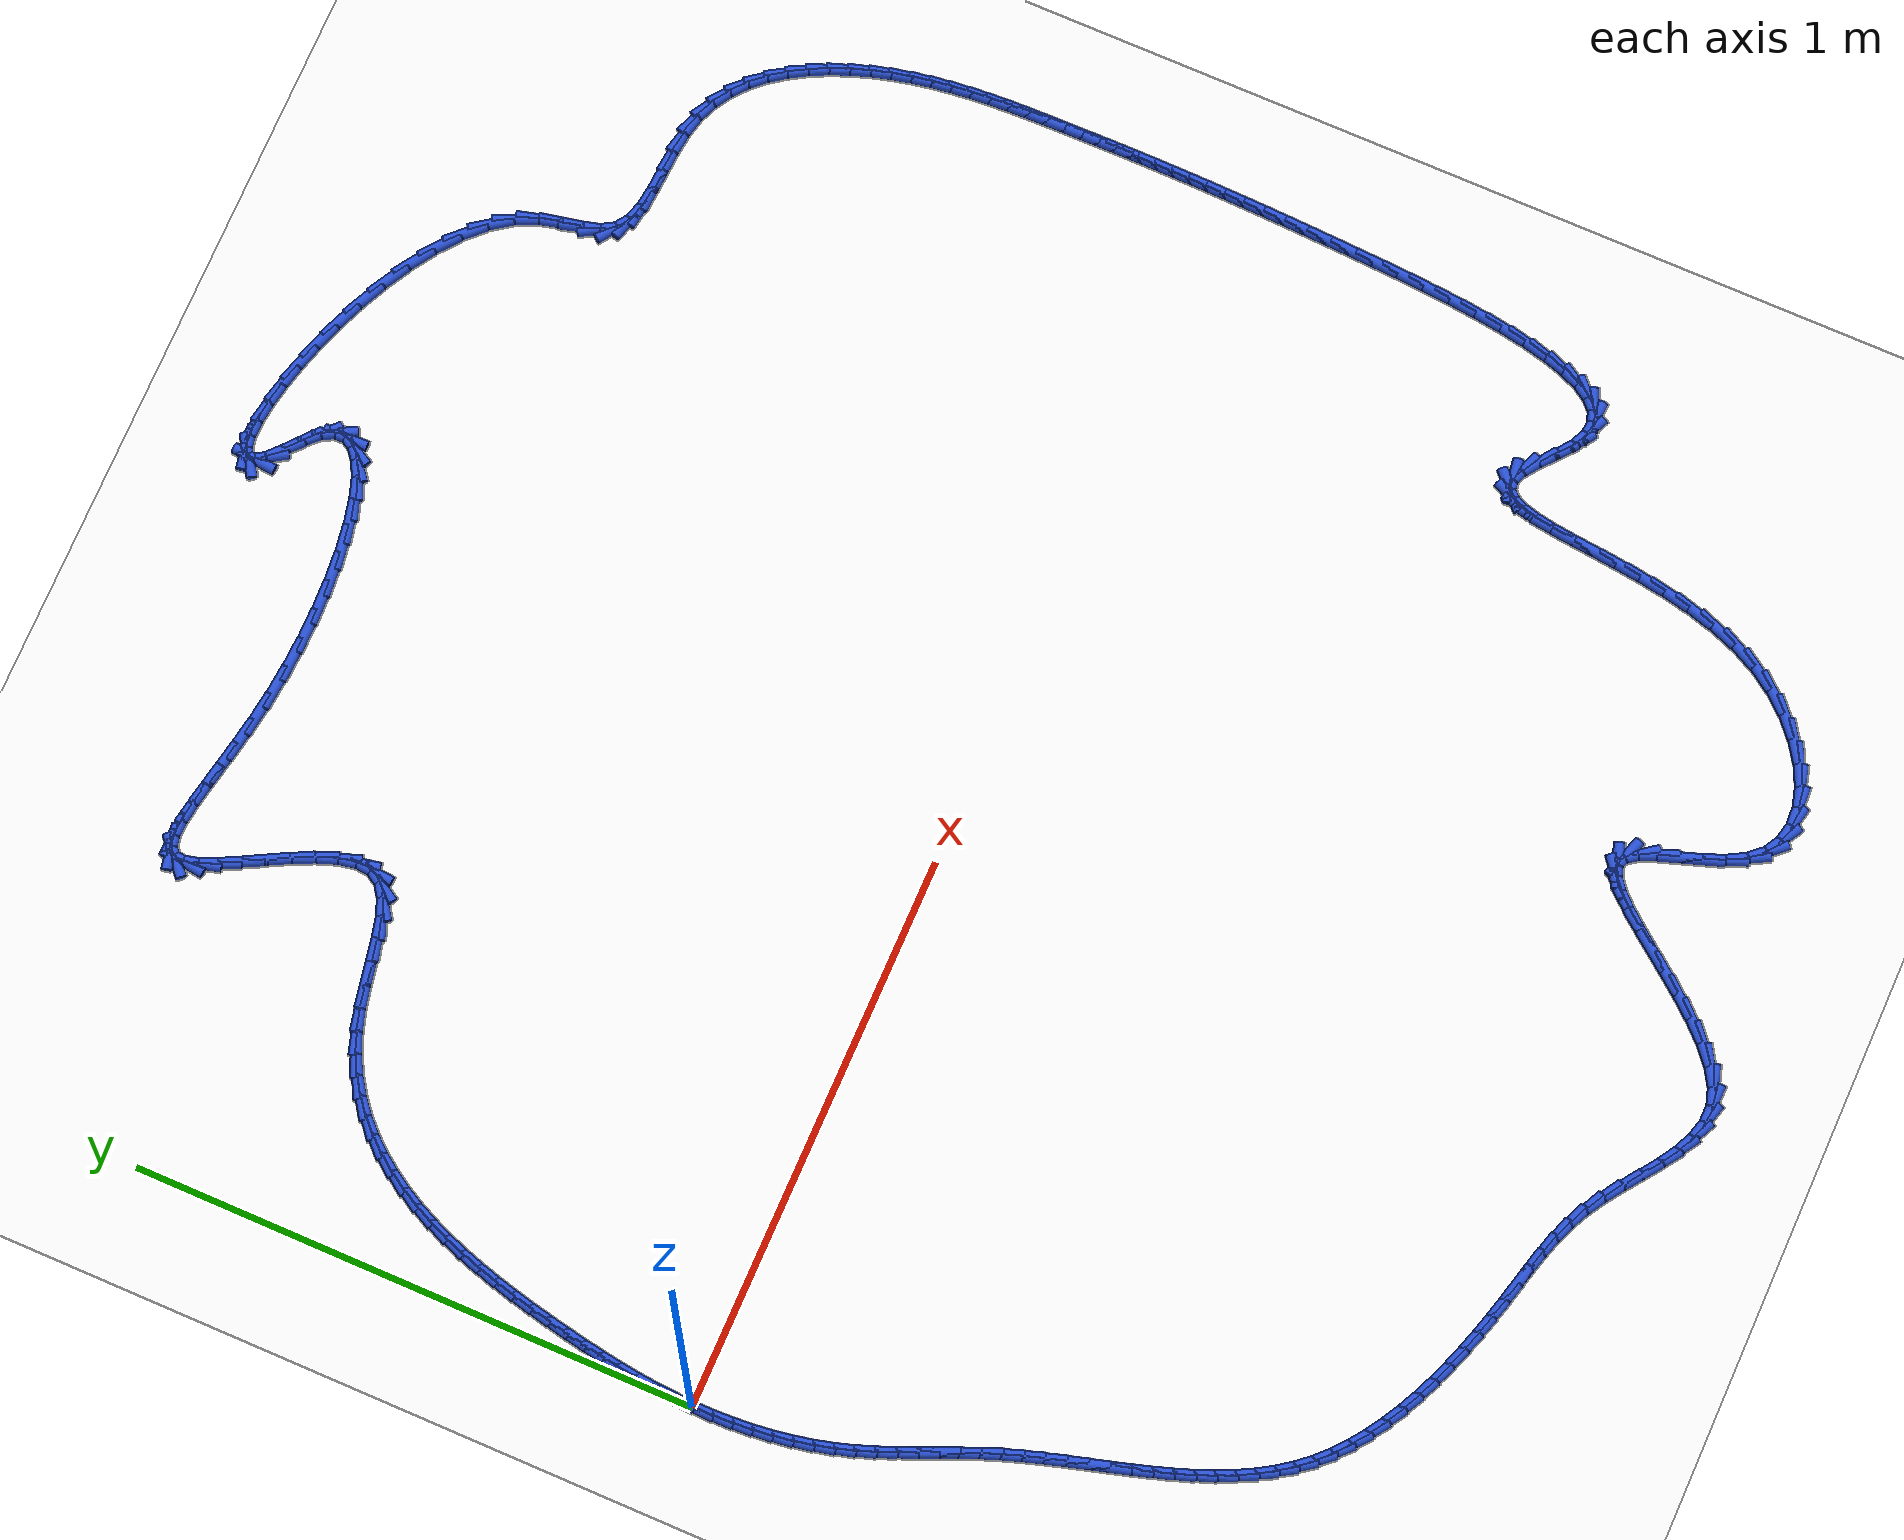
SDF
<sdf version="1.6">
 <world name="default">
  <light name="sun" type="directional">
   <pose>0 0 10 0 -0 0</pose>
   <diffuse>0.8 0.8 0.8 1</diffuse>
   <specular>0.2 0.2 0.2 1</specular>
   <attenuation>
    <range>1000</range>
    <constant>0.9</constant>
    <linear>0.01</linear>
    <quadratic>0.001</quadratic>
   </attenuation>
   <direction>-0.5 0.1 -0.9</direction>
  </light>
  <model name="ground_plane">
   <static>1</static>
   <link name="link">
    <collision name="collision">
     <geometry><plane><normal>0 0 1</normal><size>100 100</size></plane></geometry>
     <surface><friction><ode><mu>100</mu><mu2>50</mu2></ode></friction></surface>
    </collision>
    <visual name="visual">
     <cast_shadows>0</cast_shadows>
     <geometry><plane><normal>0 0 1</normal><size>100 100</size></plane></geometry>
     <material>
      <script><uri>file://media/materials/scripts/gazebo.material</uri><name>Gazebo/WhiteGlow</name></script>
     </material>
    </visual>
   </link>
  </model>
  <gravity>0 0 -9.8</gravity>
  <magnetic_field>6e-06 2.3e-05 -4.2e-05</magnetic_field>
  <atmosphere type="adiabatic"/>
  <physics name="default_physics" default="0" type="ode">
   <max_step_size>0.001</max_step_size>
   <real_time_factor>1</real_time_factor>
   <real_time_update_rate>1000</real_time_update_rate>
  </physics>
  <scene><ambient>0.4 0.4 0.4 1</ambient><background>0.7 0.7 0.7 1</background><shadows>1</shadows></scene>
  <spherical_coordinates>
   <surface_model>EARTH_WGS84</surface_model>
   <latitude_deg>0</latitude_deg>
   <longitude_deg>0</longitude_deg>
   <elevation>0</elevation>
   <heading_deg>0</heading_deg>
  </spherical_coordinates>
  <model name="line">
   <link name="link_0">
    <pose>-4.336808689942018e-18 6.245004513516506e-17 0.01 0 1.57 1.5319434057864332</pose>
    <collision name="collision">
     <geometry><cylinder><radius>0.01</radius><length>0.08</length></cylinder></geometry>
    </collision>
    <visual name="visual">
     <material>
      <script><name>Gazebo/Blue</name><uri>file://media/materials/scripts/gazebo.material</uri></script>
     </material>
     <geometry><cylinder><radius>0.01</radius><length>0.08</length></cylinder></geometry>
    </visual>
   </link>
   <link name="link_1">
    <pose>0.0013140539392554856 0.03380421931746958 0.01 0 1.57 1.4986485388361865</pose>
    <collision name="collision">
     <geometry><cylinder><radius>0.01</radius><length>0.08</length></cylinder></geometry>
    </collision>
    <visual name="visual">
     <material>
      <script><name>Gazebo/Blue</name><uri>file://media/materials/scripts/gazebo.material</uri></script>
     </material>
     <geometry><cylinder><radius>0.01</radius><length>0.08</length></cylinder></geometry>
    </visual>
   </link>
   <link name="link_2">
    <pose>0.0037434772871277416 0.06741864683966615 0.01 0 1.57 1.468514302211777</pose>
    <collision name="collision">
     <geometry><cylinder><radius>0.01</radius><length>0.08</length></cylinder></geometry>
    </collision>
    <visual name="visual">
     <material>
      <script><name>Gazebo/Blue</name><uri>file://media/materials/scripts/gazebo.material</uri></script>
     </material>
     <geometry><cylinder><radius>0.01</radius><length>0.08</length></cylinder></geometry>
    </visual>
   </link>
   <link name="link_3">
    <pose>0.007185687889429495 0.10095531708893624 0.01 0 1.57 1.441867210033133</pose>
    <collision name="collision">
     <geometry><cylinder><radius>0.01</radius><length>0.08</length></cylinder></geometry>
    </collision>
    <visual name="visual">
     <material>
      <script><name>Gazebo/Blue</name><uri>file://media/materials/scripts/gazebo.material</uri></script>
     </material>
     <geometry><cylinder><radius>0.01</radius><length>0.08</length></cylinder></geometry>
    </visual>
   </link>
   <link name="link_4">
    <pose>0.01153810359197348 0.13452626458762634 0.01 0 1.57 1.418936077674716</pose>
    <collision name="collision">
     <geometry><cylinder><radius>0.01</radius><length>0.08</length></cylinder></geometry>
    </collision>
    <visual name="visual">
     <material>
      <script><name>Gazebo/Blue</name><uri>file://media/materials/scripts/gazebo.material</uri></script>
     </material>
     <geometry><cylinder><radius>0.01</radius><length>0.08</length></cylinder></geometry>
    </visual>
   </link>
   <link name="link_5">
    <pose>0.016698142240572422 0.1682435238580828 0.01 0 1.57 1.399854854484243</pose>
    <collision name="collision">
     <geometry><cylinder><radius>0.01</radius><length>0.08</length></cylinder></geometry>
    </collision>
    <visual name="visual">
     <material>
      <script><name>Gazebo/Blue</name><uri>file://media/materials/scripts/gazebo.material</uri></script>
     </material>
     <geometry><cylinder><radius>0.01</radius><length>0.08</length></cylinder></geometry>
    </visual>
   </link>
   <link name="link_6">
    <pose>0.022563221681039053 0.20221912942265216 0.01 0 1.57 1.3846703487722567</pose>
    <collision name="collision">
     <geometry><cylinder><radius>0.01</radius><length>0.08</length></cylinder></geometry>
    </collision>
    <visual name="visual">
     <material>
      <script><name>Gazebo/Blue</name><uri>file://media/materials/scripts/gazebo.material</uri></script>
     </material>
     <geometry><cylinder><radius>0.01</radius><length>0.08</length></cylinder></geometry>
    </visual>
   </link>
   <link name="link_7">
    <pose>0.029030759759186106 0.23656511580368084 0.01 0 1.57 1.372970793227422</pose>
    <collision name="collision">
     <geometry><cylinder><radius>0.01</radius><length>0.08</length></cylinder></geometry>
    </collision>
    <visual name="visual">
     <material>
      <script><name>Gazebo/Blue</name><uri>file://media/materials/scripts/gazebo.material</uri></script>
     </material>
     <geometry><cylinder><radius>0.01</radius><length>0.08</length></cylinder></geometry>
    </visual>
   </link>
   <link name="link_8">
    <pose>0.036009167121939877 0.2713793061466617 0.01 0 1.57 1.3599854319511753</pose>
    <collision name="collision">
     <geometry><cylinder><radius>0.01</radius><length>0.08</length></cylinder></geometry>
    </collision>
    <visual name="visual">
     <material>
      <script><name>Gazebo/Blue</name><uri>file://media/materials/scripts/gazebo.material</uri></script>
     </material>
     <geometry><cylinder><radius>0.01</radius><length>0.08</length></cylinder></geometry>
    </visual>
   </link>
   <link name="link_9">
    <pose>0.04354262982971746 0.3065839945805415 0.01 0 1.57 1.3425170211216795</pose>
    <collision name="collision">
     <geometry><cylinder><radius>0.01</radius><length>0.08</length></cylinder></geometry>
    </collision>
    <visual name="visual">
     <material>
      <script><name>Gazebo/Blue</name><uri>file://media/materials/scripts/gazebo.material</uri></script>
     </material>
     <geometry><cylinder><radius>0.01</radius><length>0.08</length></cylinder></geometry>
    </visual>
   </link>
   <link name="link_10">
    <pose>0.051766877501824564 0.3419831286908846 0.01 0 1.57 1.3204099664230295</pose>
    <collision name="collision">
     <geometry><cylinder><radius>0.01</radius><length>0.08</length></cylinder></geometry>
    </collision>
    <visual name="visual">
     <material>
      <script><name>Gazebo/Blue</name><uri>file://media/materials/scripts/gazebo.material</uri></script>
     </material>
     <geometry><cylinder><radius>0.01</radius><length>0.08</length></cylinder></geometry>
    </visual>
   </link>
   <link name="link_11">
    <pose>0.06081935300771795 0.37737844119160574 0.01 0 1.57 1.2934705210745905</pose>
    <collision name="collision">
     <geometry><cylinder><radius>0.01</radius><length>0.08</length></cylinder></geometry>
    </collision>
    <visual name="visual">
     <material>
      <script><name>Gazebo/Blue</name><uri>file://media/materials/scripts/gazebo.material</uri></script>
     </material>
     <geometry><cylinder><radius>0.01</radius><length>0.08</length></cylinder></geometry>
    </visual>
   </link>
   <link name="link_12">
    <pose>0.07083749921685435 0.4125716647966196 0.01 0 1.57 1.261418212774206</pose>
    <collision name="collision">
     <geometry><cylinder><radius>0.01</radius><length>0.08</length></cylinder></geometry>
    </collision>
    <visual name="visual">
     <material>
      <script><name>Gazebo/Blue</name><uri>file://media/materials/scripts/gazebo.material</uri></script>
     </material>
     <geometry><cylinder><radius>0.01</radius><length>0.08</length></cylinder></geometry>
    </visual>
   </link>
   <link name="link_13">
    <pose>0.08195875899869054 0.44736453221984085 0.01 0 1.57 1.2238980358185412</pose>
    <collision name="collision">
     <geometry><cylinder><radius>0.01</radius><length>0.08</length></cylinder></geometry>
    </collision>
    <visual name="visual">
     <material>
      <script><name>Gazebo/Blue</name><uri>file://media/materials/scripts/gazebo.material</uri></script>
     </material>
     <geometry><cylinder><radius>0.01</radius><length>0.08</length></cylinder></geometry>
    </visual>
   </link>
   <link name="link_14">
    <pose>0.09432057522268321 0.481558776175184 0.01 0 1.57 1.1804974588891914</pose>
    <collision name="collision">
     <geometry><cylinder><radius>0.01</radius><length>0.08</length></cylinder></geometry>
    </collision>
    <visual name="visual">
     <material>
      <script><name>Gazebo/Blue</name><uri>file://media/materials/scripts/gazebo.material</uri></script>
     </material>
     <geometry><cylinder><radius>0.01</radius><length>0.08</length></cylinder></geometry>
    </visual>
   </link>
   <link name="link_15">
    <pose>0.10806039075828913 0.5149561293765638 0.01 0 1.57 1.1307727012912336</pose>
    <collision name="collision">
     <geometry><cylinder><radius>0.01</radius><length>0.08</length></cylinder></geometry>
    </collision>
    <visual name="visual">
     <material>
      <script><name>Gazebo/Blue</name><uri>file://media/materials/scripts/gazebo.material</uri></script>
     </material>
     <geometry><cylinder><radius>0.01</radius><length>0.08</length></cylinder></geometry>
    </visual>
   </link>
   <link name="link_16">
    <pose>0.12331564847496501 0.5473583245378948 0.01 0 1.57 1.0742895341842118</pose>
    <collision name="collision">
     <geometry><cylinder><radius>0.01</radius><length>0.08</length></cylinder></geometry>
    </collision>
    <visual name="visual">
     <material>
      <script><name>Gazebo/Blue</name><uri>file://media/materials/scripts/gazebo.material</uri></script>
     </material>
     <geometry><cylinder><radius>0.01</radius><length>0.08</length></cylinder></geometry>
    </visual>
   </link>
   <link name="link_17">
    <pose>0.14022379124216766 0.5785670943730917 0.01 0 1.57 1.0106839537281425</pose>
    <collision name="collision">
     <geometry><cylinder><radius>0.01</radius><length>0.08</length></cylinder></geometry>
    </collision>
    <visual name="visual">
     <material>
      <script><name>Gazebo/Blue</name><uri>file://media/materials/scripts/gazebo.material</uri></script>
     </material>
     <geometry><cylinder><radius>0.01</radius><length>0.08</length></cylinder></geometry>
    </visual>
   </link>
   <link name="link_18">
    <pose>0.15892226192935377 0.6083841715960694 0.01 0 1.57 0.9397462079947269</pose>
    <collision name="collision">
     <geometry><cylinder><radius>0.01</radius><length>0.08</length></cylinder></geometry>
    </collision>
    <visual name="visual">
     <material>
      <script><name>Gazebo/Blue</name><uri>file://media/materials/scripts/gazebo.material</uri></script>
     </material>
     <geometry><cylinder><radius>0.01</radius><length>0.08</length></cylinder></geometry>
    </visual>
   </link>
   <link name="link_19">
    <pose>0.17954850340598005 0.6366112889207419 0.01 0 1.57 0.8615261207308403</pose>
    <collision name="collision">
     <geometry><cylinder><radius>0.01</radius><length>0.08</length></cylinder></geometry>
    </collision>
    <visual name="visual">
     <material>
      <script><name>Gazebo/Blue</name><uri>file://media/materials/scripts/gazebo.material</uri></script>
     </material>
     <geometry><cylinder><radius>0.01</radius><length>0.08</length></cylinder></geometry>
    </visual>
   </link>
   <link name="link_20">
    <pose>0.20223995854150328 0.6630501790610244 0.01 0 1.57 0.7764470902443564</pose>
    <collision name="collision">
     <geometry><cylinder><radius>0.01</radius><length>0.08</length></cylinder></geometry>
    </collision>
    <visual name="visual">
     <material>
      <script><name>Gazebo/Blue</name><uri>file://media/materials/scripts/gazebo.material</uri></script>
     </material>
     <geometry><cylinder><radius>0.01</radius><length>0.08</length></cylinder></geometry>
    </visual>
   </link>
   <link name="link_21">
    <pose>0.22713407020538032 0.6875025747308313 0.01 0 1.57 0.685401648080828</pose>
    <collision name="collision">
     <geometry><cylinder><radius>0.01</radius><length>0.08</length></cylinder></geometry>
    </collision>
    <visual name="visual">
     <material>
      <script><name>Gazebo/Blue</name><uri>file://media/materials/scripts/gazebo.material</uri></script>
     </material>
     <geometry><cylinder><radius>0.01</radius><length>0.08</length></cylinder></geometry>
    </visual>
   </link>
   <link name="link_22">
    <pose>0.2543682812670676 0.7097702086440774 0.01 0 1.57 0.58978925772115</pose>
    <collision name="collision">
     <geometry><cylinder><radius>0.01</radius><length>0.08</length></cylinder></geometry>
    </collision>
    <visual name="visual">
     <material>
      <script><name>Gazebo/Blue</name><uri>file://media/materials/scripts/gazebo.material</uri></script>
     </material>
     <geometry><cylinder><radius>0.01</radius><length>0.08</length></cylinder></geometry>
    </visual>
   </link>
   <link name="link_23">
    <pose>0.2840800345960222 0.7296548135146774 0.01 0 1.57 0.49145849479141723</pose>
    <collision name="collision">
     <geometry><cylinder><radius>0.01</radius><length>0.08</length></cylinder></geometry>
    </collision>
    <visual name="visual">
     <material>
      <script><name>Gazebo/Blue</name><uri>file://media/materials/scripts/gazebo.material</uri></script>
     </material>
     <geometry><cylinder><radius>0.01</radius><length>0.08</length></cylinder></geometry>
    </visual>
   </link>
   <link name="link_24">
    <pose>0.31640677306170073 0.7469581220565455 0.01 0 1.57 0.39254038680555475</pose>
    <collision name="collision">
     <geometry><cylinder><radius>0.01</radius><length>0.08</length></cylinder></geometry>
    </collision>
    <visual name="visual">
     <material>
      <script><name>Gazebo/Blue</name><uri>file://media/materials/scripts/gazebo.material</uri></script>
     </material>
     <geometry><cylinder><radius>0.01</radius><length>0.08</length></cylinder></geometry>
    </visual>
   </link>
   <link name="link_25">
    <pose>0.3514859395335599 0.7614818669835968 0.01 0 1.57 0.2954738349655322</pose>
    <collision name="collision">
     <geometry><cylinder><radius>0.01</radius><length>0.08</length></cylinder></geometry>
    </collision>
    <visual name="visual">
     <material>
      <script><name>Gazebo/Blue</name><uri>file://media/materials/scripts/gazebo.material</uri></script>
     </material>
     <geometry><cylinder><radius>0.01</radius><length>0.08</length></cylinder></geometry>
    </visual>
   </link>
   <link name="link_26">
    <pose>0.38944411747533997 0.7730357244928493 0.01 0 1.57 0.21881490029956532</pose>
    <collision name="collision">
     <geometry><cylinder><radius>0.01</radius><length>0.08</length></cylinder></geometry>
    </collision>
    <visual name="visual">
     <material>
      <script><name>Gazebo/Blue</name><uri>file://media/materials/scripts/gazebo.material</uri></script>
     </material>
     <geometry><cylinder><radius>0.01</radius><length>0.08</length></cylinder></geometry>
    </visual>
   </link>
   <link name="link_27">
    <pose>0.4296575821303383 0.7819782093483044 0.01 0 1.57 0.18459084739233952</pose>
    <collision name="collision">
     <geometry><cylinder><radius>0.01</radius><length>0.08</length></cylinder></geometry>
    </collision>
    <visual name="visual">
     <material>
      <script><name>Gazebo/Blue</name><uri>file://media/materials/scripts/gazebo.material</uri></script>
     </material>
     <geometry><cylinder><radius>0.01</radius><length>0.08</length></cylinder></geometry>
    </visual>
   </link>
   <link name="link_28">
    <pose>0.47027899215161567 0.7895628924490602 0.01 0 1.57 0.19121079953961492</pose>
    <collision name="collision">
     <geometry><cylinder><radius>0.01</radius><length>0.08</length></cylinder></geometry>
    </collision>
    <visual name="visual">
     <material>
      <script><name>Gazebo/Blue</name><uri>file://media/materials/scripts/gazebo.material</uri></script>
     </material>
     <geometry><cylinder><radius>0.01</radius><length>0.08</length></cylinder></geometry>
    </visual>
   </link>
   <link name="link_29">
    <pose>0.5093483279760453 0.7971257670228226 0.01 0 1.57 0.24465435465526797</pose>
    <collision name="collision">
     <geometry><cylinder><radius>0.01</radius><length>0.08</length></cylinder></geometry>
    </collision>
    <visual name="visual">
     <material>
      <script><name>Gazebo/Blue</name><uri>file://media/materials/scripts/gazebo.material</uri></script>
     </material>
     <geometry><cylinder><radius>0.01</radius><length>0.08</length></cylinder></geometry>
    </visual>
   </link>
   <link name="link_30">
    <pose>0.5449055700405006 0.8060028262972974 0.01 0 1.57 0.36590014277717187</pose>
    <collision name="collision">
     <geometry><cylinder><radius>0.01</radius><length>0.08</length></cylinder></geometry>
    </collision>
    <visual name="visual">
     <material>
      <script><name>Gazebo/Blue</name><uri>file://media/materials/scripts/gazebo.material</uri></script>
     </material>
     <geometry><cylinder><radius>0.01</radius><length>0.08</length></cylinder></geometry>
    </visual>
   </link>
   <link name="link_31">
    <pose>0.5749906987818554 0.8175300635001914 0.01 0 1.57 0.6004707490488328</pose>
    <collision name="collision">
     <geometry><cylinder><radius>0.01</radius><length>0.08</length></cylinder></geometry>
    </collision>
    <visual name="visual">
     <material>
      <script><name>Gazebo/Blue</name><uri>file://media/materials/scripts/gazebo.material</uri></script>
     </material>
     <geometry><cylinder><radius>0.01</radius><length>0.08</length></cylinder></geometry>
    </visual>
   </link>
   <link name="link_32">
    <pose>0.5976436946369822 0.8330434718592097 0.01 0 1.57 1.003997543385579</pose>
    <collision name="collision">
     <geometry><cylinder><radius>0.01</radius><length>0.08</length></cylinder></geometry>
    </collision>
    <visual name="visual">
     <material>
      <script><name>Gazebo/Blue</name><uri>file://media/materials/scripts/gazebo.material</uri></script>
     </material>
     <geometry><cylinder><radius>0.01</radius><length>0.08</length></cylinder></geometry>
    </visual>
   </link>
   <link name="link_33">
    <pose>0.6109046732203666 0.8538789522892043 0.01 0 1.57 1.4696583424926406</pose>
    <collision name="collision">
     <geometry><cylinder><radius>0.01</radius><length>0.08</length></cylinder></geometry>
    </collision>
    <visual name="visual">
     <material>
      <script><name>Gazebo/Blue</name><uri>file://media/materials/scripts/gazebo.material</uri></script>
     </material>
     <geometry><cylinder><radius>0.01</radius><length>0.08</length></cylinder></geometry>
    </visual>
   </link>
   <link name="link_34">
    <pose>0.6136377213600606 0.880809715374927 0.01 0 1.57 -1.3801142799555939</pose>
    <collision name="collision">
     <geometry><cylinder><radius>0.01</radius><length>0.08</length></cylinder></geometry>
    </collision>
    <visual name="visual">
     <material>
      <script><name>Gazebo/Blue</name><uri>file://media/materials/scripts/gazebo.material</uri></script>
     </material>
     <geometry><cylinder><radius>0.01</radius><length>0.08</length></cylinder></geometry>
    </visual>
   </link>
   <link name="link_35">
    <pose>0.6074789489720074 0.912715955827897 0.01 0 1.57 -1.2227136579035274</pose>
    <collision name="collision">
     <geometry><cylinder><radius>0.01</radius><length>0.08</length></cylinder></geometry>
    </collision>
    <visual name="visual">
     <material>
      <script><name>Gazebo/Blue</name><uri>file://media/materials/scripts/gazebo.material</uri></script>
     </material>
     <geometry><cylinder><radius>0.01</radius><length>0.08</length></cylinder></geometry>
    </visual>
   </link>
   <link name="link_36">
    <pose>0.5946467747874622 0.9480802093952023 0.01 0 1.57 -1.1368525372482288</pose>
    <collision name="collision">
     <geometry><cylinder><radius>0.01</radius><length>0.08</length></cylinder></geometry>
    </collision>
    <visual name="visual">
     <material>
      <script><name>Gazebo/Blue</name><uri>file://media/materials/scripts/gazebo.material</uri></script>
     </material>
     <geometry><cylinder><radius>0.01</radius><length>0.08</length></cylinder></geometry>
    </visual>
   </link>
   <link name="link_37">
    <pose>0.5773596175376807 0.9853850118239318 0.01 0 1.57 -1.0932565484162966</pose>
    <collision name="collision">
     <geometry><cylinder><radius>0.01</radius><length>0.08</length></cylinder></geometry>
    </collision>
    <visual name="visual">
     <material>
      <script><name>Gazebo/Blue</name><uri>file://media/materials/scripts/gazebo.material</uri></script>
     </material>
     <geometry><cylinder><radius>0.01</radius><length>0.08</length></cylinder></geometry>
    </visual>
   </link>
   <link name="link_38">
    <pose>0.5578358959539181 1.0231128988611746 0.01 0 1.57 -1.080754067889779</pose>
    <collision name="collision">
     <geometry><cylinder><radius>0.01</radius><length>0.08</length></cylinder></geometry>
    </collision>
    <visual name="visual">
     <material>
      <script><name>Gazebo/Blue</name><uri>file://media/materials/scripts/gazebo.material</uri></script>
     </material>
     <geometry><cylinder><radius>0.01</radius><length>0.08</length></cylinder></geometry>
    </visual>
   </link>
   <link name="link_39">
    <pose>0.5382940287674294 1.0597464062540187 0.01 0 1.57 -1.0994013148943165</pose>
    <collision name="collision">
     <geometry><cylinder><radius>0.01</radius><length>0.08</length></cylinder></geometry>
    </collision>
    <visual name="visual">
     <material>
      <script><name>Gazebo/Blue</name><uri>file://media/materials/scripts/gazebo.material</uri></script>
     </material>
     <geometry><cylinder><radius>0.01</radius><length>0.08</length></cylinder></geometry>
    </visual>
   </link>
   <link name="link_40">
    <pose>0.5209524347094701 1.093768069749553 0.01 0 1.57 -1.162746480978303</pose>
    <collision name="collision">
     <geometry><cylinder><radius>0.01</radius><length>0.08</length></cylinder></geometry>
    </collision>
    <visual name="visual">
     <material>
      <script><name>Gazebo/Blue</name><uri>file://media/materials/scripts/gazebo.material</uri></script>
     </material>
     <geometry><cylinder><radius>0.01</radius><length>0.08</length></cylinder></geometry>
    </visual>
   </link>
   <link name="link_41">
    <pose>0.5080295325112956 1.1236604250948667 0.01 0 1.57 -1.317126105665437</pose>
    <collision name="collision">
     <geometry><cylinder><radius>0.01</radius><length>0.08</length></cylinder></geometry>
    </collision>
    <visual name="visual">
     <material>
      <script><name>Gazebo/Blue</name><uri>file://media/materials/scripts/gazebo.material</uri></script>
     </material>
     <geometry><cylinder><radius>0.01</radius><length>0.08</length></cylinder></geometry>
    </visual>
   </link>
   <link name="link_42">
    <pose>0.5017437409041609 1.1479060080370476 0.01 0 1.57 1.4295170453533816</pose>
    <collision name="collision">
     <geometry><cylinder><radius>0.01</radius><length>0.08</length></cylinder></geometry>
    </collision>
    <visual name="visual">
     <material>
      <script><name>Gazebo/Blue</name><uri>file://media/materials/scripts/gazebo.material</uri></script>
     </material>
     <geometry><cylinder><radius>0.01</radius><length>0.08</length></cylinder></geometry>
    </visual>
   </link>
   <link name="link_43">
    <pose>0.5041882209099134 1.1650932027344842 0.01 0 1.57 0.7205648410267232</pose>
    <collision name="collision">
     <geometry><cylinder><radius>0.01</radius><length>0.08</length></cylinder></geometry>
    </collision>
    <visual name="visual">
     <material>
      <script><name>Gazebo/Blue</name><uri>file://media/materials/scripts/gazebo.material</uri></script>
     </material>
     <geometry><cylinder><radius>0.01</radius><length>0.08</length></cylinder></geometry>
    </visual>
   </link>
   <link name="link_44">
    <pose>0.5157540189764507 1.1752487568950367 0.01 0 1.57 0.20792350350129915</pose>
    <collision name="collision">
     <geometry><cylinder><radius>0.01</radius><length>0.08</length></cylinder></geometry>
    </collision>
    <visual name="visual">
     <material>
      <script><name>Gazebo/Blue</name><uri>file://media/materials/scripts/gazebo.material</uri></script>
     </material>
     <geometry><cylinder><radius>0.01</radius><length>0.08</length></cylinder></geometry>
    </visual>
   </link>
   <link name="link_45">
    <pose>0.5356046899413384 1.179436703974895 0.01 0 1.57 -0.025393909594070493</pose>
    <collision name="collision">
     <geometry><cylinder><radius>0.01</radius><length>0.08</length></cylinder></geometry>
    </collision>
    <visual name="visual">
     <material>
      <script><name>Gazebo/Blue</name><uri>file://media/materials/scripts/gazebo.material</uri></script>
     </material>
     <geometry><cylinder><radius>0.01</radius><length>0.08</length></cylinder></geometry>
    </visual>
   </link>
   <link name="link_46">
    <pose>0.5628766468522989 1.1787440134662697 0.01 0 1.57 -0.1318468066890831</pose>
    <collision name="collision">
     <geometry><cylinder><radius>0.01</radius><length>0.08</length></cylinder></geometry>
    </collision>
    <visual name="visual">
     <material>
      <script><name>Gazebo/Blue</name><uri>file://media/materials/scripts/gazebo.material</uri></script>
     </material>
     <geometry><cylinder><radius>0.01</radius><length>0.08</length></cylinder></geometry>
    </visual>
   </link>
   <link name="link_47">
    <pose>0.5967063027570535 1.1742576548613701 0.01 0 1.57 -0.1800229171772811</pose>
    <collision name="collision">
     <geometry><cylinder><radius>0.01</radius><length>0.08</length></cylinder></geometry>
    </collision>
    <visual name="visual">
     <material>
      <script><name>Gazebo/Blue</name><uri>file://media/materials/scripts/gazebo.material</uri></script>
     </material>
     <geometry><cylinder><radius>0.01</radius><length>0.08</length></cylinder></geometry>
    </visual>
   </link>
   <link name="link_48">
    <pose>0.6362300707033254 1.1670645976524077 0.01 0 1.57 -0.19613631826651462</pose>
    <collision name="collision">
     <geometry><cylinder><radius>0.01</radius><length>0.08</length></cylinder></geometry>
    </collision>
    <visual name="visual">
     <material>
      <script><name>Gazebo/Blue</name><uri>file://media/materials/scripts/gazebo.material</uri></script>
     </material>
     <geometry><cylinder><radius>0.01</radius><length>0.08</length></cylinder></geometry>
    </visual>
   </link>
   <link name="link_49">
    <pose>0.6805843637388361 1.1582518113315916 0.01 0 1.57 -0.19104581190082603</pose>
    <collision name="collision">
     <geometry><cylinder><radius>0.01</radius><length>0.08</length></cylinder></geometry>
    </collision>
    <visual name="visual">
     <material>
      <script><name>Gazebo/Blue</name><uri>file://media/materials/scripts/gazebo.material</uri></script>
     </material>
     <geometry><cylinder><radius>0.01</radius><length>0.08</length></cylinder></geometry>
    </visual>
   </link>
   <link name="link_50">
    <pose>0.7289055949113081 1.148906265391133 0.01 0 1.57 -0.16931906644913652</pose>
    <collision name="collision">
     <geometry><cylinder><radius>0.01</radius><length>0.08</length></cylinder></geometry>
    </collision>
    <visual name="visual">
     <material>
      <script><name>Gazebo/Blue</name><uri>file://media/materials/scripts/gazebo.material</uri></script>
     </material>
     <geometry><cylinder><radius>0.01</radius><length>0.08</length></cylinder></geometry>
    </visual>
   </link>
   <link name="link_51">
    <pose>0.7803301772684634 1.140114929323241 0.01 0 1.57 -0.13250731604007934</pose>
    <collision name="collision">
     <geometry><cylinder><radius>0.01</radius><length>0.08</length></cylinder></geometry>
    </collision>
    <visual name="visual">
     <material>
      <script><name>Gazebo/Blue</name><uri>file://media/materials/scripts/gazebo.material</uri></script>
     </material>
     <geometry><cylinder><radius>0.01</radius><length>0.08</length></cylinder></geometry>
    </visual>
   </link>
   <link name="link_52">
    <pose>0.833994074479671 1.1329621580142335 0.01 0 1.57 -0.08667703356944327</pose>
    <collision name="collision">
     <geometry><cylinder><radius>0.01</radius><length>0.08</length></cylinder></geometry>
    </collision>
    <visual name="visual">
     <material>
      <script><name>Gazebo/Blue</name><uri>file://media/materials/scripts/gazebo.material</uri></script>
     </material>
     <geometry><cylinder><radius>0.01</radius><length>0.08</length></cylinder></geometry>
    </visual>
   </link>
   <link name="link_53">
    <pose>0.8889735120391729 1.128184733345039 0.01 0 1.57 -0.042647658393842006</pose>
    <collision name="collision">
     <geometry><cylinder><radius>0.01</radius><length>0.08</length></cylinder></geometry>
    </collision>
    <visual name="visual">
     <material>
      <script><name>Gazebo/Blue</name><uri>file://media/materials/scripts/gazebo.material</uri></script>
     </material>
     <geometry><cylinder><radius>0.01</radius><length>0.08</length></cylinder></geometry>
    </visual>
   </link>
   <link name="link_54">
    <pose>0.9442256922156741 1.1258269275890662 0.01 0 1.57 0.0004411157891163632</pose>
    <collision name="collision">
     <geometry><cylinder><radius>0.01</radius><length>0.08</length></cylinder></geometry>
    </collision>
    <visual name="visual">
     <material>
      <script><name>Gazebo/Blue</name><uri>file://media/materials/scripts/gazebo.material</uri></script>
     </material>
     <geometry><cylinder><radius>0.01</radius><length>0.08</length></cylinder></geometry>
    </visual>
   </link>
   <link name="link_55">
    <pose>0.9986937136553328 1.1258509542948836 0.01 0 1.57 0.044966996668675846</pose>
    <collision name="collision">
     <geometry><cylinder><radius>0.01</radius><length>0.08</length></cylinder></geometry>
    </collision>
    <visual name="visual">
     <material>
      <script><name>Gazebo/Blue</name><uri>file://media/materials/scripts/gazebo.material</uri></script>
     </material>
     <geometry><cylinder><radius>0.01</radius><length>0.08</length></cylinder></geometry>
    </visual>
   </link>
   <link name="link_56">
    <pose>1.051320675004307 1.1282190270110597 0.01 0 1.57 0.09372073595957132</pose>
    <collision name="collision">
     <geometry><cylinder><radius>0.01</radius><length>0.08</length></cylinder></geometry>
    </collision>
    <visual name="visual">
     <material>
      <script><name>Gazebo/Blue</name><uri>file://media/materials/scripts/gazebo.material</uri></script>
     </material>
     <geometry><cylinder><radius>0.01</radius><length>0.08</length></cylinder></geometry>
    </visual>
   </link>
   <link name="link_57">
    <pose>1.1010496749087553 1.132893359286163 0.01 0 1.57 0.15052796607002553</pose>
    <collision name="collision">
     <geometry><cylinder><radius>0.01</radius><length>0.08</length></cylinder></geometry>
    </collision>
    <visual name="visual">
     <material>
      <script><name>Gazebo/Blue</name><uri>file://media/materials/scripts/gazebo.material</uri></script>
     </material>
     <geometry><cylinder><radius>0.01</radius><length>0.08</length></cylinder></geometry>
    </visual>
   </link>
   <link name="link_58">
    <pose>1.1468238120148364 1.1398361646687618 0.01 0 1.57 0.22136016469763864</pose>
    <collision name="collision">
     <geometry><cylinder><radius>0.01</radius><length>0.08</length></cylinder></geometry>
    </collision>
    <visual name="visual">
     <material>
      <script><name>Gazebo/Blue</name><uri>file://media/materials/scripts/gazebo.material</uri></script>
     </material>
     <geometry><cylinder><radius>0.01</radius><length>0.08</length></cylinder></geometry>
    </visual>
   </link>
   <link name="link_59">
    <pose>1.1875861849687084 1.149009656707424 0.01 0 1.57 0.31660080765306786</pose>
    <collision name="collision">
     <geometry><cylinder><radius>0.01</radius><length>0.08</length></cylinder></geometry>
    </collision>
    <visual name="visual">
     <material>
      <script><name>Gazebo/Blue</name><uri>file://media/materials/scripts/gazebo.material</uri></script>
     </material>
     <geometry><cylinder><radius>0.01</radius><length>0.08</length></cylinder></geometry>
    </visual>
   </link>
   <link name="link_60">
    <pose>1.2222798924165295 1.1603760489507189 0.01 0 1.57 0.4559992652802266</pose>
    <collision name="collision">
     <geometry><cylinder><radius>0.01</radius><length>0.08</length></cylinder></geometry>
    </collision>
    <visual name="visual">
     <material>
      <script><name>Gazebo/Blue</name><uri>file://media/materials/scripts/gazebo.material</uri></script>
     </material>
     <geometry><cylinder><radius>0.01</radius><length>0.08</length></cylinder></geometry>
    </visual>
   </link>
   <link name="link_61">
    <pose>1.2498480330044583 1.1738975549472137 0.01 0 1.57 0.6788258323478273</pose>
    <collision name="collision">
     <geometry><cylinder><radius>0.01</radius><length>0.08</length></cylinder></geometry>
    </collision>
    <visual name="visual">
     <material>
      <script><name>Gazebo/Blue</name><uri>file://media/materials/scripts/gazebo.material</uri></script>
     </material>
     <geometry><cylinder><radius>0.01</radius><length>0.08</length></cylinder></geometry>
    </visual>
   </link>
   <link name="link_62">
    <pose>1.2692337053786533 1.1895363882454777 0.01 0 1.57 1.050735204315759</pose>
    <collision name="collision">
     <geometry><cylinder><radius>0.01</radius><length>0.08</length></cylinder></geometry>
    </collision>
    <visual name="visual">
     <material>
      <script><name>Gazebo/Blue</name><uri>file://media/materials/scripts/gazebo.material</uri></script>
     </material>
     <geometry><cylinder><radius>0.01</radius><length>0.08</length></cylinder></geometry>
    </visual>
   </link>
   <link name="link_63">
    <pose>1.279380008185273 1.2072547623940793 0.01 0 1.57 -1.5632070423842848</pose>
    <collision name="collision">
     <geometry><cylinder><radius>0.01</radius><length>0.08</length></cylinder></geometry>
    </collision>
    <visual name="visual">
     <material>
      <script><name>Gazebo/Blue</name><uri>file://media/materials/scripts/gazebo.material</uri></script>
     </material>
     <geometry><cylinder><radius>0.01</radius><length>0.08</length></cylinder></geometry>
    </visual>
   </link>
   <link name="link_64">
    <pose>1.279230040070475 1.2270148909415857 0.01 0 1.57 -1.0845802407968343</pose>
    <collision name="collision">
     <geometry><cylinder><radius>0.01</radius><length>0.08</length></cylinder></geometry>
    </collision>
    <visual name="visual">
     <material>
      <script><name>Gazebo/Blue</name><uri>file://media/materials/scripts/gazebo.material</uri></script>
     </material>
     <geometry><cylinder><radius>0.01</radius><length>0.08</length></cylinder></geometry>
    </visual>
   </link>
   <link name="link_65">
    <pose>1.2677268996804183 1.248778987436567 0.01 0 1.57 -0.7967105602884467</pose>
    <collision name="collision">
     <geometry><cylinder><radius>0.01</radius><length>0.08</length></cylinder></geometry>
    </collision>
    <visual name="visual">
     <material>
      <script><name>Gazebo/Blue</name><uri>file://media/materials/scripts/gazebo.material</uri></script>
     </material>
     <geometry><cylinder><radius>0.01</radius><length>0.08</length></cylinder></geometry>
    </visual>
   </link>
   <link name="link_66">
    <pose>1.2447308782711284 1.2723012647522993 0.01 0 1.57 -0.7028440234331017</pose>
    <collision name="collision">
     <geometry><cylinder><radius>0.01</radius><length>0.08</length></cylinder></geometry>
    </collision>
    <visual name="visual">
     <material>
      <script><name>Gazebo/Blue</name><uri>file://media/materials/scripts/gazebo.material</uri></script>
     </material>
     <geometry><cylinder><radius>0.01</radius><length>0.08</length></cylinder></geometry>
    </visual>
   </link>
   <link name="link_67">
    <pose>1.2170356798543405 1.295763578418855 0.01 0 1.57 -0.7489956851390467</pose>
    <collision name="collision">
     <geometry><cylinder><radius>0.01</radius><length>0.08</length></cylinder></geometry>
    </collision>
    <visual name="visual">
     <material>
      <script><name>Gazebo/Blue</name><uri>file://media/materials/scripts/gazebo.material</uri></script>
     </material>
     <geometry><cylinder><radius>0.01</radius><length>0.08</length></cylinder></geometry>
    </visual>
   </link>
   <link name="link_68">
    <pose>1.1945890412983757 1.316632718423587 0.01 0 1.57 -1.007700589777862</pose>
    <collision name="collision">
     <geometry><cylinder><radius>0.01</radius><length>0.08</length></cylinder></geometry>
    </collision>
    <visual name="visual">
     <material>
      <script><name>Gazebo/Blue</name><uri>file://media/materials/scripts/gazebo.material</uri></script>
     </material>
     <geometry><cylinder><radius>0.01</radius><length>0.08</length></cylinder></geometry>
    </visual>
   </link>
   <link name="link_69">
    <pose>1.1841703237047616 1.3331370815878667 0.01 0 1.57 1.4637179778415383</pose>
    <collision name="collision">
     <geometry><cylinder><radius>0.01</radius><length>0.08</length></cylinder></geometry>
    </collision>
    <visual name="visual">
     <material>
      <script><name>Gazebo/Blue</name><uri>file://media/materials/scripts/gazebo.material</uri></script>
     </material>
     <geometry><cylinder><radius>0.01</radius><length>0.08</length></cylinder></geometry>
    </visual>
   </link>
   <link name="link_70">
    <pose>1.1854679362446843 1.345209077287086 0.01 0 1.57 0.5863482554093195</pose>
    <collision name="collision">
     <geometry><cylinder><radius>0.01</radius><length>0.08</length></cylinder></geometry>
    </collision>
    <visual name="visual">
     <material>
      <script><name>Gazebo/Blue</name><uri>file://media/materials/scripts/gazebo.material</uri></script>
     </material>
     <geometry><cylinder><radius>0.01</radius><length>0.08</length></cylinder></geometry>
    </visual>
   </link>
   <link name="link_71">
    <pose>1.197213082221624 1.3530111391347608 0.01 0 1.57 0.17477007311011628</pose>
    <collision name="collision">
     <geometry><cylinder><radius>0.01</radius><length>0.08</length></cylinder></geometry>
    </collision>
    <visual name="visual">
     <material>
      <script><name>Gazebo/Blue</name><uri>file://media/materials/scripts/gazebo.material</uri></script>
     </material>
     <geometry><cylinder><radius>0.01</radius><length>0.08</length></cylinder></geometry>
    </visual>
   </link>
   <link name="link_72">
    <pose>1.2181369649390634 1.356705700744409 0.01 0 1.57 -0.008687669150396234</pose>
    <collision name="collision">
     <geometry><cylinder><radius>0.01</radius><length>0.08</length></cylinder></geometry>
    </collision>
    <visual name="visual">
     <material>
      <script><name>Gazebo/Blue</name><uri>file://media/materials/scripts/gazebo.material</uri></script>
     </material>
     <geometry><cylinder><radius>0.01</radius><length>0.08</length></cylinder></geometry>
    </visual>
   </link>
   <link name="link_73">
    <pose>1.2469707877004825 1.3564551957295465 0.01 0 1.57 -0.11320363131416397</pose>
    <collision name="collision">
     <geometry><cylinder><radius>0.01</radius><length>0.08</length></cylinder></geometry>
    </collision>
    <visual name="visual">
     <material>
      <script><name>Gazebo/Blue</name><uri>file://media/materials/scripts/gazebo.material</uri></script>
     </material>
     <geometry><cylinder><radius>0.01</radius><length>0.08</length></cylinder></geometry>
    </visual>
   </link>
   <link name="link_74">
    <pose>1.2824457538093637 1.3524220577036903 0.01 0 1.57 -0.18521707449150657</pose>
    <collision name="collision">
     <geometry><cylinder><radius>0.01</radius><length>0.08</length></cylinder></geometry>
    </collision>
    <visual name="visual">
     <material>
      <script><name>Gazebo/Blue</name><uri>file://media/materials/scripts/gazebo.material</uri></script>
     </material>
     <geometry><cylinder><radius>0.01</radius><length>0.08</length></cylinder></geometry>
    </visual>
   </link>
   <link name="link_75">
    <pose>1.3232930665691873 1.344768720280356 0.01 0 1.57 -0.24232591253080182</pose>
    <collision name="collision">
     <geometry><cylinder><radius>0.01</radius><length>0.08</length></cylinder></geometry>
    </collision>
    <visual name="visual">
     <material>
      <script><name>Gazebo/Blue</name><uri>file://media/materials/scripts/gazebo.material</uri></script>
     </material>
     <geometry><cylinder><radius>0.01</radius><length>0.08</length></cylinder></geometry>
    </visual>
   </link>
   <link name="link_76">
    <pose>1.3682439292834352 1.3336576170730612 0.01 0 1.57 -0.29281457367207847</pose>
    <collision name="collision">
     <geometry><cylinder><radius>0.01</radius><length>0.08</length></cylinder></geometry>
    </collision>
    <visual name="visual">
     <material>
      <script><name>Gazebo/Blue</name><uri>file://media/materials/scripts/gazebo.material</uri></script>
     </material>
     <geometry><cylinder><radius>0.01</radius><length>0.08</length></cylinder></geometry>
    </visual>
   </link>
   <link name="link_77">
    <pose>1.4160295452555884 1.3192511816953223 0.01 0 1.57 -0.3414735196073798</pose>
    <collision name="collision">
     <geometry><cylinder><radius>0.01</radius><length>0.08</length></cylinder></geometry>
    </collision>
    <visual name="visual">
     <material>
      <script><name>Gazebo/Blue</name><uri>file://media/materials/scripts/gazebo.material</uri></script>
     </material>
     <geometry><cylinder><radius>0.01</radius><length>0.08</length></cylinder></geometry>
    </visual>
   </link>
   <link name="link_78">
    <pose>1.465381117789128 1.301711847760656 0.01 0 1.57 -0.39174663160890816</pose>
    <collision name="collision">
     <geometry><cylinder><radius>0.01</radius><length>0.08</length></cylinder></geometry>
    </collision>
    <visual name="visual">
     <material>
      <script><name>Gazebo/Blue</name><uri>file://media/materials/scripts/gazebo.material</uri></script>
     </material>
     <geometry><cylinder><radius>0.01</radius><length>0.08</length></cylinder></geometry>
    </visual>
   </link>
   <link name="link_79">
    <pose>1.5150298501875354 1.2812020488825786 0.01 0 1.57 -0.44673200243471844</pose>
    <collision name="collision">
     <geometry><cylinder><radius>0.01</radius><length>0.08</length></cylinder></geometry>
    </collision>
    <visual name="visual">
     <material>
      <script><name>Gazebo/Blue</name><uri>file://media/materials/scripts/gazebo.material</uri></script>
     </material>
     <geometry><cylinder><radius>0.01</radius><length>0.08</length></cylinder></geometry>
    </visual>
   </link>
   <link name="link_80">
    <pose>1.5637069457542918 1.2578842186746064 0.01 0 1.57 -0.5098142421383467</pose>
    <collision name="collision">
     <geometry><cylinder><radius>0.01</radius><length>0.08</length></cylinder></geometry>
    </collision>
    <visual name="visual">
     <material>
      <script><name>Gazebo/Blue</name><uri>file://media/materials/scripts/gazebo.material</uri></script>
     </material>
     <geometry><cylinder><radius>0.01</radius><length>0.08</length></cylinder></geometry>
    </visual>
   </link>
   <link name="link_81">
    <pose>1.6101436077928788 1.231920790750257 0.01 0 1.57 -0.5852284826661662</pose>
    <collision name="collision">
     <geometry><cylinder><radius>0.01</radius><length>0.08</length></cylinder></geometry>
    </collision>
    <visual name="visual">
     <material>
      <script><name>Gazebo/Blue</name><uri>file://media/materials/scripts/gazebo.material</uri></script>
     </material>
     <geometry><cylinder><radius>0.01</radius><length>0.08</length></cylinder></geometry>
    </visual>
   </link>
   <link name="link_82">
    <pose>1.6530710396067767 1.203474198723046 0.01 0 1.57 -0.6786890689363886</pose>
    <collision name="collision">
     <geometry><cylinder><radius>0.01</radius><length>0.08</length></cylinder></geometry>
    </collision>
    <visual name="visual">
     <material>
      <script><name>Gazebo/Blue</name><uri>file://media/materials/scripts/gazebo.material</uri></script>
     </material>
     <geometry><cylinder><radius>0.01</radius><length>0.08</length></cylinder></geometry>
    </visual>
   </link>
   <link name="link_83">
    <pose>1.691220444499468 1.1727068762064907 0.01 0 1.57 -0.7980541213603082</pose>
    <collision name="collision">
     <geometry><cylinder><radius>0.01</radius><length>0.08</length></cylinder></geometry>
    </collision>
    <visual name="visual">
     <material>
      <script><name>Gazebo/Blue</name><uri>file://media/materials/scripts/gazebo.material</uri></script>
     </material>
     <geometry><cylinder><radius>0.01</radius><length>0.08</length></cylinder></geometry>
    </visual>
   </link>
   <link name="link_84">
    <pose>1.723323025774433 1.1397812568141075 0.01 0 1.57 -0.9535292715406037</pose>
    <collision name="collision">
     <geometry><cylinder><radius>0.01</radius><length>0.08</length></cylinder></geometry>
    </collision>
    <visual name="visual">
     <material>
      <script><name>Gazebo/Blue</name><uri>file://media/materials/scripts/gazebo.material</uri></script>
     </material>
     <geometry><cylinder><radius>0.01</radius><length>0.08</length></cylinder></geometry>
    </visual>
   </link>
   <link name="link_85">
    <pose>1.748109986735153 1.1048597741594124 0.01 0 1.57 -1.1501669128799297</pose>
    <collision name="collision">
     <geometry><cylinder><radius>0.01</radius><length>0.08</length></cylinder></geometry>
    </collision>
    <visual name="visual">
     <material>
      <script><name>Gazebo/Blue</name><uri>file://media/materials/scripts/gazebo.material</uri></script>
     </material>
     <geometry><cylinder><radius>0.01</radius><length>0.08</length></cylinder></geometry>
    </visual>
   </link>
   <link name="link_86">
    <pose>1.7645138994703802 1.068188866166791 0.01 0 1.57 -1.3112420724312892</pose>
    <collision name="collision">
     <geometry><cylinder><radius>0.01</radius><length>0.08</length></cylinder></geometry>
    </collision>
    <visual name="visual">
     <material>
      <script><name>Gazebo/Blue</name><uri>file://media/materials/scripts/gazebo.material</uri></script>
     </material>
     <geometry><cylinder><radius>0.01</radius><length>0.08</length></cylinder></geometry>
    </visual>
   </link>
   <link name="link_87">
    <pose>1.7743332815994968 1.031210547219831 0.01 0 1.57 -1.3685661899801613</pose>
    <collision name="collision">
     <geometry><cylinder><radius>0.01</radius><length>0.08</length></cylinder></geometry>
    </collision>
    <visual name="visual">
     <material>
      <script><name>Gazebo/Blue</name><uri>file://media/materials/scripts/gazebo.material</uri></script>
     </material>
     <geometry><cylinder><radius>0.01</radius><length>0.08</length></cylinder></geometry>
    </visual>
   </link>
   <link name="link_88">
    <pose>1.7814999538293654 0.9962567742793507 0.01 0 1.57 -1.299750616894385</pose>
    <collision name="collision">
     <geometry><cylinder><radius>0.01</radius><length>0.08</length></cylinder></geometry>
    </collision>
    <visual name="visual">
     <material>
      <script><name>Gazebo/Blue</name><uri>file://media/materials/scripts/gazebo.material</uri></script>
     </material>
     <geometry><cylinder><radius>0.01</radius><length>0.08</length></cylinder></geometry>
    </visual>
   </link>
   <link name="link_89">
    <pose>1.7899965619599243 0.9656807068322338 0.01 0 1.57 -1.0458874950703692</pose>
    <collision name="collision">
     <geometry><cylinder><radius>0.01</radius><length>0.08</length></cylinder></geometry>
    </collision>
    <visual name="visual">
     <material>
      <script><name>Gazebo/Blue</name><uri>file://media/materials/scripts/gazebo.material</uri></script>
     </material>
     <geometry><cylinder><radius>0.01</radius><length>0.08</length></cylinder></geometry>
    </visual>
   </link>
   <link name="link_90">
    <pose>1.8038054250348166 0.9418352521529635 0.01 0 1.57 -0.621070327525698</pose>
    <collision name="collision">
     <geometry><cylinder><radius>0.01</radius><length>0.08</length></cylinder></geometry>
    </collision>
    <visual name="visual">
     <material>
      <script><name>Gazebo/Blue</name><uri>file://media/materials/scripts/gazebo.material</uri></script>
     </material>
     <geometry><cylinder><radius>0.01</radius><length>0.08</length></cylinder></geometry>
    </visual>
   </link>
   <link name="link_91">
    <pose>1.8257194138330552 0.9261552216497192 0.01 0 1.57 -0.3034674328019627</pose>
    <collision name="collision">
     <geometry><cylinder><radius>0.01</radius><length>0.08</length></cylinder></geometry>
    </collision>
    <visual name="visual">
     <material>
      <script><name>Gazebo/Blue</name><uri>file://media/materials/scripts/gazebo.material</uri></script>
     </material>
     <geometry><cylinder><radius>0.01</radius><length>0.08</length></cylinder></geometry>
    </visual>
   </link>
   <link name="link_92">
    <pose>1.8546651219940231 0.917091174985199 0.01 0 1.57 -0.13409178280921627</pose>
    <collision name="collision">
     <geometry><cylinder><radius>0.01</radius><length>0.08</length></cylinder></geometry>
    </collision>
    <visual name="visual">
     <material>
      <script><name>Gazebo/Blue</name><uri>file://media/materials/scripts/gazebo.material</uri></script>
     </material>
     <geometry><cylinder><radius>0.01</radius><length>0.08</length></cylinder></geometry>
    </visual>
   </link>
   <link name="link_93">
    <pose>1.8887849358783473 0.9124883681007382 0.01 0 1.57 -0.06126239321919002</pose>
    <collision name="collision">
     <geometry><cylinder><radius>0.01</radius><length>0.08</length></cylinder></geometry>
    </collision>
    <visual name="visual">
     <material>
      <script><name>Gazebo/Blue</name><uri>file://media/materials/scripts/gazebo.material</uri></script>
     </material>
     <geometry><cylinder><radius>0.01</radius><length>0.08</length></cylinder></geometry>
    </visual>
   </link>
   <link name="link_94">
    <pose>1.9262212418466547 0.9101920569376701 0.01 0 1.57 -0.05508111813115847</pose>
    <collision name="collision">
     <geometry><cylinder><radius>0.01</radius><length>0.08</length></cylinder></geometry>
    </collision>
    <visual name="visual">
     <material>
      <script><name>Gazebo/Blue</name><uri>file://media/materials/scripts/gazebo.material</uri></script>
     </material>
     <geometry><cylinder><radius>0.01</radius><length>0.08</length></cylinder></geometry>
    </visual>
   </link>
   <link name="link_95">
    <pose>1.9651164262595713 0.9080474974373295 0.01 0 1.57 -0.10732457470055283</pose>
    <collision name="collision">
     <geometry><cylinder><radius>0.01</radius><length>0.08</length></cylinder></geometry>
    </collision>
    <visual name="visual">
     <material>
      <script><name>Gazebo/Blue</name><uri>file://media/materials/scripts/gazebo.material</uri></script>
     </material>
     <geometry><cylinder><radius>0.01</radius><length>0.08</length></cylinder></geometry>
    </visual>
   </link>
   <link name="link_96">
    <pose>2.003612875477724 0.9038999455410502 0.01 0 1.57 -0.2245457225120204</pose>
    <collision name="collision">
     <geometry><cylinder><radius>0.01</radius><length>0.08</length></cylinder></geometry>
    </collision>
    <visual name="visual">
     <material>
      <script><name>Gazebo/Blue</name><uri>file://media/materials/scripts/gazebo.material</uri></script>
     </material>
     <geometry><cylinder><radius>0.01</radius><length>0.08</length></cylinder></geometry>
    </visual>
   </link>
   <link name="link_97">
    <pose>2.0398705247348117 0.8956187946949907 0.01 0 1.57 -0.3871573613724709</pose>
    <collision name="collision">
     <geometry><cylinder><radius>0.01</radius><length>0.08</length></cylinder></geometry>
    </collision>
    <visual name="visual">
     <material>
      <script><name>Gazebo/Blue</name><uri>file://media/materials/scripts/gazebo.material</uri></script>
     </material>
     <geometry><cylinder><radius>0.01</radius><length>0.08</length></cylinder></geometry>
    </visual>
   </link>
   <link name="link_98">
    <pose>2.0728483942066416 0.8821725355105136 0.01 0 1.57 -0.5466565688693179</pose>
    <collision name="collision">
     <geometry><cylinder><radius>0.01</radius><length>0.08</length></cylinder></geometry>
    </collision>
    <visual name="visual">
     <material>
      <script><name>Gazebo/Blue</name><uri>file://media/materials/scripts/gazebo.material</uri></script>
     </material>
     <geometry><cylinder><radius>0.01</radius><length>0.08</length></cylinder></geometry>
    </visual>
   </link>
   <link name="link_99">
    <pose>2.102616723183298 0.8640580790635152 0.01 0 1.57 -0.6928245263786239</pose>
    <collision name="collision">
     <geometry><cylinder><radius>0.01</radius><length>0.08</length></cylinder></geometry>
    </collision>
    <visual name="visual">
     <material>
      <script><name>Gazebo/Blue</name><uri>file://media/materials/scripts/gazebo.material</uri></script>
     </material>
     <geometry><cylinder><radius>0.01</radius><length>0.08</length></cylinder></geometry>
    </visual>
   </link>
   <link name="link_100">
    <pose>2.1293278622825698 0.8418852760221116 0.01 0 1.57 -0.8221020304431803</pose>
    <collision name="collision">
     <geometry><cylinder><radius>0.01</radius><length>0.08</length></cylinder></geometry>
    </collision>
    <visual name="visual">
     <material>
      <script><name>Gazebo/Blue</name><uri>file://media/materials/scripts/gazebo.material</uri></script>
     </material>
     <geometry><cylinder><radius>0.01</radius><length>0.08</length></cylinder></geometry>
    </visual>
   </link>
   <link name="link_101">
    <pose>2.1531341621222455 0.8162639770544197 0.01 0 1.57 -0.9338746706398564</pose>
    <collision name="collision">
     <geometry><cylinder><radius>0.01</radius><length>0.08</length></cylinder></geometry>
    </collision>
    <visual name="visual">
     <material>
      <script><name>Gazebo/Blue</name><uri>file://media/materials/scripts/gazebo.material</uri></script>
     </material>
     <geometry><cylinder><radius>0.01</radius><length>0.08</length></cylinder></geometry>
    </visual>
   </link>
   <link name="link_102">
    <pose>2.174187973320114 0.7878040328285557 0.01 0 1.57 -1.0294087001116023</pose>
    <collision name="collision">
     <geometry><cylinder><radius>0.01</radius><length>0.08</length></cylinder></geometry>
    </collision>
    <visual name="visual">
     <material>
      <script><name>Gazebo/Blue</name><uri>file://media/materials/scripts/gazebo.material</uri></script>
     </material>
     <geometry><cylinder><radius>0.01</radius><length>0.08</length></cylinder></geometry>
    </visual>
   </link>
   <link name="link_103">
    <pose>2.192641646493964 0.7571152940126362 0.01 0 1.57 -1.110819088437704</pose>
    <collision name="collision">
     <geometry><cylinder><radius>0.01</radius><length>0.08</length></cylinder></geometry>
    </collision>
    <visual name="visual">
     <material>
      <script><name>Gazebo/Blue</name><uri>file://media/materials/scripts/gazebo.material</uri></script>
     </material>
     <geometry><cylinder><radius>0.01</radius><length>0.08</length></cylinder></geometry>
    </visual>
   </link>
   <link name="link_104">
    <pose>2.2086475322615846 0.7248076112747781 0.01 0 1.57 -1.1804027094474792</pose>
    <collision name="collision">
     <geometry><cylinder><radius>0.01</radius><length>0.08</length></cylinder></geometry>
    </collision>
    <visual name="visual">
     <material>
      <script><name>Gazebo/Blue</name><uri>file://media/materials/scripts/gazebo.material</uri></script>
     </material>
     <geometry><cylinder><radius>0.01</radius><length>0.08</length></cylinder></geometry>
    </visual>
   </link>
   <link name="link_105">
    <pose>2.2223579998884144 0.6914905662198797 0.01 0 1.57 -1.2411940380463125</pose>
    <collision name="collision">
     <geometry><cylinder><radius>0.01</radius><length>0.08</length></cylinder></geometry>
    </collision>
    <visual name="visual">
     <material>
      <script><name>Gazebo/Blue</name><uri>file://media/materials/scripts/gazebo.material</uri></script>
     </material>
     <geometry><cylinder><radius>0.01</radius><length>0.08</length></cylinder></geometry>
    </visual>
   </link>
   <link name="link_106">
    <pose>2.2339339424836546 0.6576507516133844 0.01 0 1.57 -1.296427701397356</pose>
    <collision name="collision">
     <geometry><cylinder><radius>0.01</radius><length>0.08</length></cylinder></geometry>
    </collision>
    <visual name="visual">
     <material>
      <script><name>Gazebo/Blue</name><uri>file://media/materials/scripts/gazebo.material</uri></script>
     </material>
     <geometry><cylinder><radius>0.01</radius><length>0.08</length></cylinder></geometry>
    </visual>
   </link>
   <link name="link_107">
    <pose>2.243558248748905 0.6234573902105164 0.01 0 1.57 -1.3463678781463506</pose>
    <collision name="collision">
     <geometry><cylinder><radius>0.01</radius><length>0.08</length></cylinder></geometry>
    </collision>
    <visual name="visual">
     <material>
      <script><name>Gazebo/Blue</name><uri>file://media/materials/scripts/gazebo.material</uri></script>
     </material>
     <geometry><cylinder><radius>0.01</radius><length>0.08</length></cylinder></geometry>
    </visual>
   </link>
   <link name="link_108">
    <pose>2.2514173075244597 0.5890292019642024 0.01 0 1.57 -1.3909591024430785</pose>
    <collision name="collision">
     <geometry><cylinder><radius>0.01</radius><length>0.08</length></cylinder></geometry>
    </collision>
    <visual name="visual">
     <material>
      <script><name>Gazebo/Blue</name><uri>file://media/materials/scripts/gazebo.material</uri></script>
     </material>
     <geometry><cylinder><radius>0.01</radius><length>0.08</length></cylinder></geometry>
    </visual>
   </link>
   <link name="link_109">
    <pose>2.2576975076506174 0.5544849068273692 0.01 0 1.57 -1.4302271881954076</pose>
    <collision name="collision">
     <geometry><cylinder><radius>0.01</radius><length>0.08</length></cylinder></geometry>
    </collision>
    <visual name="visual">
     <material>
      <script><name>Gazebo/Blue</name><uri>file://media/materials/scripts/gazebo.material</uri></script>
     </material>
     <geometry><cylinder><radius>0.01</radius><length>0.08</length></cylinder></geometry>
    </visual>
   </link>
   <link name="link_110">
    <pose>2.2625852379676723 0.5199432247529437 0.01 0 1.57 -1.4642400373870224</pose>
    <collision name="collision">
     <geometry><cylinder><radius>0.01</radius><length>0.08</length></cylinder></geometry>
    </collision>
    <visual name="visual">
     <material>
      <script><name>Gazebo/Blue</name><uri>file://media/materials/scripts/gazebo.material</uri></script>
     </material>
     <geometry><cylinder><radius>0.01</radius><length>0.08</length></cylinder></geometry>
    </visual>
   </link>
   <link name="link_111">
    <pose>2.266266887315922 0.4855228756938525 0.01 0 1.57 -1.4930733345964429</pose>
    <collision name="collision">
     <geometry><cylinder><radius>0.01</radius><length>0.08</length></cylinder></geometry>
    </collision>
    <visual name="visual">
     <material>
      <script><name>Gazebo/Blue</name><uri>file://media/materials/scripts/gazebo.material</uri></script>
     </material>
     <geometry><cylinder><radius>0.01</radius><length>0.08</length></cylinder></geometry>
    </visual>
   </link>
   <link name="link_112">
    <pose>2.2689288445356617 0.4513425796030223 0.01 0 1.57 -1.516781162360011</pose>
    <collision name="collision">
     <geometry><cylinder><radius>0.01</radius><length>0.08</length></cylinder></geometry>
    </collision>
    <visual name="visual">
     <material>
      <script><name>Gazebo/Blue</name><uri>file://media/materials/scripts/gazebo.material</uri></script>
     </material>
     <geometry><cylinder><radius>0.01</radius><length>0.08</length></cylinder></geometry>
    </visual>
   </link>
   <link name="link_113">
    <pose>2.270757498467189 0.41752105643338 0.01 0 1.57 -1.535370342874431</pose>
    <collision name="collision">
     <geometry><cylinder><radius>0.01</radius><length>0.08</length></cylinder></geometry>
    </collision>
    <visual name="visual">
     <material>
      <script><name>Gazebo/Blue</name><uri>file://media/materials/scripts/gazebo.material</uri></script>
     </material>
     <geometry><cylinder><radius>0.01</radius><length>0.08</length></cylinder></geometry>
    </visual>
   </link>
   <link name="link_114">
    <pose>2.2719392379507983 0.38417702613785243 0.01 0 1.57 -1.548776620946159</pose>
    <collision name="collision">
     <geometry><cylinder><radius>0.01</radius><length>0.08</length></cylinder></geometry>
    </collision>
    <visual name="visual">
     <material>
      <script><name>Gazebo/Blue</name><uri>file://media/materials/scripts/gazebo.material</uri></script>
     </material>
     <geometry><cylinder><radius>0.01</radius><length>0.08</length></cylinder></geometry>
    </visual>
   </link>
   <link name="link_115">
    <pose>2.272660451826787 0.351429208669366 0.01 0 1.57 -1.5568404159464497</pose>
    <collision name="collision">
     <geometry><cylinder><radius>0.01</radius><length>0.08</length></cylinder></geometry>
    </collision>
    <visual name="visual">
     <material>
      <script><name>Gazebo/Blue</name><uri>file://media/materials/scripts/gazebo.material</uri></script>
     </material>
     <geometry><cylinder><radius>0.01</radius><length>0.08</length></cylinder></geometry>
    </visual>
   </link>
   <link name="link_116">
    <pose>2.2731075289354514 0.3193963239808477 0.01 0 1.57 -1.5598694993901652</pose>
    <collision name="collision">
     <geometry><cylinder><radius>0.01</radius><length>0.08</length></cylinder></geometry>
    </collision>
    <visual name="visual">
     <material>
      <script><name>Gazebo/Blue</name><uri>file://media/materials/scripts/gazebo.material</uri></script>
     </material>
     <geometry><cylinder><radius>0.01</radius><length>0.08</length></cylinder></geometry>
    </visual>
   </link>
   <link name="link_117">
    <pose>2.273448784130913 0.2881666173823809 0.01 0 1.57 -1.5617682558393209</pose>
    <collision name="collision">
     <geometry><cylinder><radius>0.01</radius><length>0.08</length></cylinder></geometry>
    </collision>
    <visual name="visual">
     <material>
      <script><name>Gazebo/Blue</name><uri>file://media/materials/scripts/gazebo.material</uri></script>
     </material>
     <geometry><cylinder><radius>0.01</radius><length>0.08</length></cylinder></geometry>
    </visual>
   </link>
   <link name="link_118">
    <pose>2.2737246346912645 0.2576126854105982 0.01 0 1.57 -1.5642948234435514</pose>
    <collision name="collision">
     <geometry><cylinder><radius>0.01</radius><length>0.08</length></cylinder></geometry>
    </collision>
    <visual name="visual">
     <material>
      <script><name>Gazebo/Blue</name><uri>file://media/materials/scripts/gazebo.material</uri></script>
     </material>
     <geometry><cylinder><radius>0.01</radius><length>0.08</length></cylinder></geometry>
    </visual>
   </link>
   <link name="link_119">
    <pose>2.273920323536049 0.22751409482692447 0.01 0 1.57 -1.5674293252845697</pose>
    <collision name="collision">
     <geometry><cylinder><radius>0.01</radius><length>0.08</length></cylinder></geometry>
    </collision>
    <visual name="visual">
     <material>
      <script><name>Gazebo/Blue</name><uri>file://media/materials/scripts/gazebo.material</uri></script>
     </material>
     <geometry><cylinder><radius>0.01</radius><length>0.08</length></cylinder></geometry>
    </visual>
   </link>
   <link name="link_120">
    <pose>2.274020876213928 0.19765004588260118 0.01 0 1.57 1.570476131092246</pose>
    <collision name="collision">
     <geometry><cylinder><radius>0.01</radius><length>0.08</length></cylinder></geometry>
    </collision>
    <visual name="visual">
     <material>
      <script><name>Gazebo/Blue</name><uri>file://media/materials/scripts/gazebo.material</uri></script>
     </material>
     <geometry><cylinder><radius>0.01</radius><length>0.08</length></cylinder></geometry>
    </visual>
   </link>
   <link name="link_121">
    <pose>2.2740113182735597 0.16779973882886837 0.01 0 1.57 1.5663168220290515</pose>
    <collision name="collision">
     <geometry><cylinder><radius>0.01</radius><length>0.08</length></cylinder></geometry>
    </collision>
    <visual name="visual">
     <material>
      <script><name>Gazebo/Blue</name><uri>file://media/materials/scripts/gazebo.material</uri></script>
     </material>
     <geometry><cylinder><radius>0.01</radius><length>0.08</length></cylinder></geometry>
    </visual>
   </link>
   <link name="link_122">
    <pose>2.2738766752636064 0.13774237391696717 0.01 0 1.57 1.5617855644180827</pose>
    <collision name="collision">
     <geometry><cylinder><radius>0.01</radius><length>0.08</length></cylinder></geometry>
    </collision>
    <visual name="visual">
     <material>
      <script><name>Gazebo/Blue</name><uri>file://media/materials/scripts/gazebo.material</uri></script>
     </material>
     <geometry><cylinder><radius>0.01</radius><length>0.08</length></cylinder></geometry>
    </visual>
   </link>
   <link name="link_123">
    <pose>2.273601972732727 0.10725715139813857 0.01 0 1.57 1.5569943458974227</pose>
    <collision name="collision">
     <geometry><cylinder><radius>0.01</radius><length>0.08</length></cylinder></geometry>
    </collision>
    <visual name="visual">
     <material>
      <script><name>Gazebo/Blue</name><uri>file://media/materials/scripts/gazebo.material</uri></script>
     </material>
     <geometry><cylinder><radius>0.01</radius><length>0.08</length></cylinder></geometry>
    </visual>
   </link>
   <link name="link_124">
    <pose>2.2731722362295828 0.0761232715236233 0.01 0 1.57 1.5520584453760513</pose>
    <collision name="collision">
     <geometry><cylinder><radius>0.01</radius><length>0.08</length></cylinder></geometry>
    </collision>
    <visual name="visual">
     <material>
      <script><name>Gazebo/Blue</name><uri>file://media/materials/scripts/gazebo.material</uri></script>
     </material>
     <geometry><cylinder><radius>0.01</radius><length>0.08</length></cylinder></geometry>
    </visual>
   </link>
   <link name="link_125">
    <pose>2.2725724913028333 0.04411993454466227 0.01 0 1.57 1.5470883917432983</pose>
    <collision name="collision">
     <geometry><cylinder><radius>0.01</radius><length>0.08</length></cylinder></geometry>
    </collision>
    <visual name="visual">
     <material>
      <script><name>Gazebo/Blue</name><uri>file://media/materials/scripts/gazebo.material</uri></script>
     </material>
     <geometry><cylinder><radius>0.01</radius><length>0.08</length></cylinder></geometry>
    </visual>
   </link>
   <link name="link_126">
    <pose>2.27178776350114 0.011026340712496294 0.01 0 1.57 1.5421834392581335</pose>
    <collision name="collision">
     <geometry><cylinder><radius>0.01</radius><length>0.08</length></cylinder></geometry>
    </collision>
    <visual name="visual">
     <material>
      <script><name>Gazebo/Blue</name><uri>file://media/materials/scripts/gazebo.material</uri></script>
     </material>
     <geometry><cylinder><radius>0.01</radius><length>0.08</length></cylinder></geometry>
    </visual>
   </link>
   <link name="link_127">
    <pose>2.2708030783731625 -0.023378309721633794 0.01 0 1.57 1.5374271509549273</pose>
    <collision name="collision">
     <geometry><cylinder><radius>0.01</radius><length>0.08</length></cylinder></geometry>
    </collision>
    <visual name="visual">
     <material>
      <script><name>Gazebo/Blue</name><uri>file://media/materials/scripts/gazebo.material</uri></script>
     </material>
     <geometry><cylinder><radius>0.01</radius><length>0.08</length></cylinder></geometry>
    </visual>
   </link>
   <link name="link_128">
    <pose>2.2696034614675615 -0.05931481650648718 0.01 0 1.57 1.5328852113017062</pose>
    <collision name="collision">
     <geometry><cylinder><radius>0.01</radius><length>0.08</length></cylinder></geometry>
    </collision>
    <visual name="visual">
     <material>
      <script><name>Gazebo/Blue</name><uri>file://media/materials/scripts/gazebo.material</uri></script>
     </material>
     <geometry><cylinder><radius>0.01</radius><length>0.08</length></cylinder></geometry>
    </visual>
   </link>
   <link name="link_129">
    <pose>2.268173938332997 -0.09700397939082293 0.01 0 1.57 1.5286052103125436</pose>
    <collision name="collision">
     <geometry><cylinder><radius>0.01</radius><length>0.08</length></cylinder></geometry>
    </collision>
    <visual name="visual">
     <material>
      <script><name>Gazebo/Blue</name><uri>file://media/materials/scripts/gazebo.material</uri></script>
     </material>
     <geometry><cylinder><radius>0.01</radius><length>0.08</length></cylinder></geometry>
    </visual>
   </link>
   <link name="link_130">
    <pose>2.266499534518129 -0.13666659812340026 0.01 0 1.57 1.5246179180766588</pose>
    <collision name="collision">
     <geometry><cylinder><radius>0.01</radius><length>0.08</length></cylinder></geometry>
    </collision>
    <visual name="visual">
     <material>
      <script><name>Gazebo/Blue</name><uri>file://media/materials/scripts/gazebo.material</uri></script>
     </material>
     <geometry><cylinder><radius>0.01</radius><length>0.08</length></cylinder></geometry>
    </visual>
   </link>
   <link name="link_131">
    <pose>2.2645652755716186 -0.17852347245297834 0.01 0 1.57 1.5209395018729328</pose>
    <collision name="collision">
     <geometry><cylinder><radius>0.01</radius><length>0.08</length></cylinder></geometry>
    </collision>
    <visual name="visual">
     <material>
      <script><name>Gazebo/Blue</name><uri>file://media/materials/scripts/gazebo.material</uri></script>
     </material>
     <geometry><cylinder><radius>0.01</radius><length>0.08</length></cylinder></geometry>
    </visual>
   </link>
   <link name="link_132">
    <pose>2.2623561870421254 -0.22279540212831628 0.01 0 1.57 1.517217216244969</pose>
    <collision name="collision">
     <geometry><cylinder><radius>0.01</radius><length>0.08</length></cylinder></geometry>
    </collision>
    <visual name="visual">
     <material>
      <script><name>Gazebo/Blue</name><uri>file://media/materials/scripts/gazebo.material</uri></script>
     </material>
     <geometry><cylinder><radius>0.01</radius><length>0.08</length></cylinder></geometry>
    </visual>
   </link>
   <link name="link_133">
    <pose>2.2598449969739054 -0.2696193715266864 0.01 0 1.57 1.51049156796722</pose>
    <collision name="collision">
     <geometry><cylinder><radius>0.01</radius><length>0.08</length></cylinder></geometry>
    </collision>
    <visual name="visual">
     <material>
      <script><name>Gazebo/Blue</name><uri>file://media/materials/scripts/gazebo.material</uri></script>
     </material>
     <geometry><cylinder><radius>0.01</radius><length>0.08</length></cylinder></geometry>
    </visual>
   </link>
   <link name="link_134">
    <pose>2.2568989223644285 -0.31841323964107243 0.01 0 1.57 1.4993058086925917</pose>
    <collision name="collision">
     <geometry><cylinder><radius>0.01</radius><length>0.08</length></cylinder></geometry>
    </collision>
    <visual name="visual">
     <material>
      <script><name>Gazebo/Blue</name><uri>file://media/materials/scripts/gazebo.material</uri></script>
     </material>
     <geometry><cylinder><radius>0.01</radius><length>0.08</length></cylinder></geometry>
    </visual>
   </link>
   <link name="link_135">
    <pose>2.253331492037457 -0.3682289461628271 0.01 0 1.57 1.4833076357004709</pose>
    <collision name="collision">
     <geometry><cylinder><radius>0.01</radius><length>0.08</length></cylinder></geometry>
    </collision>
    <visual name="visual">
     <material>
      <script><name>Gazebo/Blue</name><uri>file://media/materials/scripts/gazebo.material</uri></script>
     </material>
     <geometry><cylinder><radius>0.01</radius><length>0.08</length></cylinder></geometry>
    </visual>
   </link>
   <link name="link_136">
    <pose>2.2489558098264157 -0.4181155342018657 0.01 0 1.57 1.4616377518656896</pose>
    <collision name="collision">
     <geometry><cylinder><radius>0.01</radius><length>0.08</length></cylinder></geometry>
    </collision>
    <visual name="visual">
     <material>
      <script><name>Gazebo/Blue</name><uri>file://media/materials/scripts/gazebo.material</uri></script>
     </material>
     <geometry><cylinder><radius>0.01</radius><length>0.08</length></cylinder></geometry>
    </visual>
   </link>
   <link name="link_137">
    <pose>2.243584979564726 -0.46712204686810355 0.01 0 1.57 1.4327752378607934</pose>
    <collision name="collision">
     <geometry><cylinder><radius>0.01</radius><length>0.08</length></cylinder></geometry>
    </collision>
    <visual name="visual">
     <material>
      <script><name>Gazebo/Blue</name><uri>file://media/materials/scripts/gazebo.material</uri></script>
     </material>
     <geometry><cylinder><radius>0.01</radius><length>0.08</length></cylinder></geometry>
    </visual>
   </link>
   <link name="link_138">
    <pose>2.237032105085813 -0.5142975272714562 0.01 0 1.57 1.3942095951741276</pose>
    <collision name="collision">
     <geometry><cylinder><radius>0.01</radius><length>0.08</length></cylinder></geometry>
    </collision>
    <visual name="visual">
     <material>
      <script><name>Gazebo/Blue</name><uri>file://media/materials/scripts/gazebo.material</uri></script>
     </material>
     <geometry><cylinder><radius>0.01</radius><length>0.08</length></cylinder></geometry>
    </visual>
   </link>
   <link name="link_139">
    <pose>2.2291102902230993 -0.5586910185218387 0.01 0 1.57 1.3417931940346643</pose>
    <collision name="collision">
     <geometry><cylinder><radius>0.01</radius><length>0.08</length></cylinder></geometry>
    </collision>
    <visual name="visual">
     <material>
      <script><name>Gazebo/Blue</name><uri>file://media/materials/scripts/gazebo.material</uri></script>
     </material>
     <geometry><cylinder><radius>0.01</radius><length>0.08</length></cylinder></geometry>
    </visual>
   </link>
   <link name="link_140">
    <pose>2.2196326388100087 -0.5993515637291669 0.01 0 1.57 1.2684766781677497</pose>
    <collision name="collision">
     <geometry><cylinder><radius>0.01</radius><length>0.08</length></cylinder></geometry>
    </collision>
    <visual name="visual">
     <material>
      <script><name>Gazebo/Blue</name><uri>file://media/materials/scripts/gazebo.material</uri></script>
     </material>
     <geometry><cylinder><radius>0.01</radius><length>0.08</length></cylinder></geometry>
    </visual>
   </link>
   <link name="link_141">
    <pose>2.208412254679965 -0.6353282060033557 0.01 0 1.57 1.1618355766898376</pose>
    <collision name="collision">
     <geometry><cylinder><radius>0.01</radius><length>0.08</length></cylinder></geometry>
    </collision>
    <visual name="visual">
     <material>
      <script><name>Gazebo/Blue</name><uri>file://media/materials/scripts/gazebo.material</uri></script>
     </material>
     <geometry><cylinder><radius>0.01</radius><length>0.08</length></cylinder></geometry>
    </visual>
   </link>
   <link name="link_142">
    <pose>2.195262241666391 -0.6656699884543209 0.01 0 1.57 0.9996123819713505</pose>
    <collision name="collision">
     <geometry><cylinder><radius>0.01</radius><length>0.08</length></cylinder></geometry>
    </collision>
    <visual name="visual">
     <material>
      <script><name>Gazebo/Blue</name><uri>file://media/materials/scripts/gazebo.material</uri></script>
     </material>
     <geometry><cylinder><radius>0.01</radius><length>0.08</length></cylinder></geometry>
    </visual>
   </link>
   <link name="link_143">
    <pose>2.179995703602711 -0.6894259541919776 0.01 0 1.57 0.7454430825202889</pose>
    <collision name="collision">
     <geometry><cylinder><radius>0.01</radius><length>0.08</length></cylinder></geometry>
    </collision>
    <visual name="visual">
     <material>
      <script><name>Gazebo/Blue</name><uri>file://media/materials/scripts/gazebo.material</uri></script>
     </material>
     <geometry><cylinder><radius>0.01</radius><length>0.08</length></cylinder></geometry>
    </visual>
   </link>
   <link name="link_144">
    <pose>2.162425744322349 -0.7056451463262414 0.01 0 1.57 0.3678671859137303</pose>
    <collision name="collision">
     <geometry><cylinder><radius>0.01</radius><length>0.08</length></cylinder></geometry>
    </collision>
    <visual name="visual">
     <material>
      <script><name>Gazebo/Blue</name><uri>file://media/materials/scripts/gazebo.material</uri></script>
     </material>
     <geometry><cylinder><radius>0.01</radius><length>0.08</length></cylinder></geometry>
    </visual>
   </link>
   <link name="link_145">
    <pose>2.142365467658728 -0.7133766079670276 0.01 0 1.57 -0.0749435534714723</pose>
    <collision name="collision">
     <geometry><cylinder><radius>0.01</radius><length>0.08</length></cylinder></geometry>
    </collision>
    <visual name="visual">
     <material>
      <script><name>Gazebo/Blue</name><uri>file://media/materials/scripts/gazebo.material</uri></script>
     </material>
     <geometry><cylinder><radius>0.01</radius><length>0.08</length></cylinder></geometry>
    </visual>
   </link>
   <link name="link_146">
    <pose>2.119627977445271 -0.7116693822242518 0.01 0 1.57 -0.4410867007547526</pose>
    <collision name="collision">
     <geometry><cylinder><radius>0.01</radius><length>0.08</length></cylinder></geometry>
    </collision>
    <visual name="visual">
     <material>
      <script><name>Gazebo/Blue</name><uri>file://media/materials/scripts/gazebo.material</uri></script>
     </material>
     <geometry><cylinder><radius>0.01</radius><length>0.08</length></cylinder></geometry>
    </visual>
   </link>
   <link name="link_147">
    <pose>2.094030464380516 -0.6995845721171847 0.01 0 1.57 -0.6470558447896223</pose>
    <collision name="collision">
     <geometry><cylinder><radius>0.01</radius><length>0.08</length></cylinder></geometry>
    </collision>
    <visual name="visual">
     <material>
      <script><name>Gazebo/Blue</name><uri>file://media/materials/scripts/gazebo.material</uri></script>
     </material>
     <geometry><cylinder><radius>0.01</radius><length>0.08</length></cylinder></geometry>
    </visual>
   </link>
   <link name="link_148">
    <pose>2.0661925195732187 -0.6785510799303778 0.01 0 1.57 -0.7006280040195979</pose>
    <collision name="collision">
     <geometry><cylinder><radius>0.01</radius><length>0.08</length></cylinder></geometry>
    </collision>
    <visual name="visual">
     <material>
      <script><name>Gazebo/Blue</name><uri>file://media/materials/scripts/gazebo.material</uri></script>
     </material>
     <geometry><cylinder><radius>0.01</radius><length>0.08</length></cylinder></geometry>
    </visual>
   </link>
   <link name="link_149">
    <pose>2.038493535001295 -0.6551907953297033 0.01 0 1.57 -0.6349154006253478</pose>
    <collision name="collision">
     <geometry><cylinder><radius>0.01</radius><length>0.08</length></cylinder></geometry>
    </collision>
    <visual name="visual">
     <material>
      <script><name>Gazebo/Blue</name><uri>file://media/materials/scripts/gazebo.material</uri></script>
     </material>
     <geometry><cylinder><radius>0.01</radius><length>0.08</length></cylinder></geometry>
    </visual>
   </link>
   <link name="link_150">
    <pose>2.0135454871162595 -0.6368123084891202 0.01 0 1.57 -0.37528190863316485</pose>
    <collision name="collision">
     <geometry><cylinder><radius>0.01</radius><length>0.08</length></cylinder></geometry>
    </collision>
    <visual name="visual">
     <material>
      <script><name>Gazebo/Blue</name><uri>file://media/materials/scripts/gazebo.material</uri></script>
     </material>
     <geometry><cylinder><radius>0.01</radius><length>0.08</length></cylinder></geometry>
    </visual>
   </link>
   <link name="link_151">
    <pose>1.993198938195167 -0.6287967407760975 0.01 0 1.57 0.14096237516827245</pose>
    <collision name="collision">
     <geometry><cylinder><radius>0.01</radius><length>0.08</length></cylinder></geometry>
    </collision>
    <visual name="visual">
     <material>
      <script><name>Gazebo/Blue</name><uri>file://media/materials/scripts/gazebo.material</uri></script>
     </material>
     <geometry><cylinder><radius>0.01</radius><length>0.08</length></cylinder></geometry>
    </visual>
   </link>
   <link name="link_152">
    <pose>1.9771510378941621 -0.6310739942433858 0.01 0 1.57 0.7484120509855717</pose>
    <collision name="collision">
     <geometry><cylinder><radius>0.01</radius><length>0.08</length></cylinder></geometry>
    </collision>
    <visual name="visual">
     <material>
      <script><name>Gazebo/Blue</name><uri>file://media/materials/scripts/gazebo.material</uri></script>
     </material>
     <geometry><cylinder><radius>0.01</radius><length>0.08</length></cylinder></geometry>
    </visual>
   </link>
   <link name="link_153">
    <pose>1.9647209155291352 -0.6426170378598762 0.01 0 1.57 1.1233605883638536</pose>
    <collision name="collision">
     <geometry><cylinder><radius>0.01</radius><length>0.08</length></cylinder></geometry>
    </collision>
    <visual name="visual">
     <material>
      <script><name>Gazebo/Blue</name><uri>file://media/materials/scripts/gazebo.material</uri></script>
     </material>
     <geometry><cylinder><radius>0.01</radius><length>0.08</length></cylinder></geometry>
    </visual>
   </link>
   <link name="link_154">
    <pose>1.9552277004159735 -0.6623988405944582 0.01 0 1.57 1.3088488796414934</pose>
    <collision name="collision">
     <geometry><cylinder><radius>0.01</radius><length>0.08</length></cylinder></geometry>
    </collision>
    <visual name="visual">
     <material>
      <script><name>Gazebo/Blue</name><uri>file://media/materials/scripts/gazebo.material</uri></script>
     </material>
     <geometry><cylinder><radius>0.01</radius><length>0.08</length></cylinder></geometry>
    </visual>
   </link>
   <link name="link_155">
    <pose>1.9479905218705675 -0.689392371416023 0.01 0 1.57 1.4017701582260922</pose>
    <collision name="collision">
     <geometry><cylinder><radius>0.01</radius><length>0.08</length></cylinder></geometry>
    </collision>
    <visual name="visual">
     <material>
      <script><name>Gazebo/Blue</name><uri>file://media/materials/scripts/gazebo.material</uri></script>
     </material>
     <geometry><cylinder><radius>0.01</radius><length>0.08</length></cylinder></geometry>
    </visual>
   </link>
   <link name="link_156">
    <pose>1.9423285092088052 -0.7225705992934606 0.01 0 1.57 1.447064710460334</pose>
    <collision name="collision">
     <geometry><cylinder><radius>0.01</radius><length>0.08</length></cylinder></geometry>
    </collision>
    <visual name="visual">
     <material>
      <script><name>Gazebo/Blue</name><uri>file://media/materials/scripts/gazebo.material</uri></script>
     </material>
     <geometry><cylinder><radius>0.01</radius><length>0.08</length></cylinder></geometry>
    </visual>
   </link>
   <link name="link_157">
    <pose>1.937560791746576 -0.7609064931956615 0.01 0 1.57 1.4639603687491611</pose>
    <collision name="collision">
     <geometry><cylinder><radius>0.01</radius><length>0.08</length></cylinder></geometry>
    </collision>
    <visual name="visual">
     <material>
      <script><name>Gazebo/Blue</name><uri>file://media/materials/scripts/gazebo.material</uri></script>
     </material>
     <geometry><cylinder><radius>0.01</radius><length>0.08</length></cylinder></geometry>
    </visual>
   </link>
   <link name="link_158">
    <pose>1.9330064987997695 -0.8033730220915163 0.01 0 1.57 1.4610411363811038</pose>
    <collision name="collision">
     <geometry><cylinder><radius>0.01</radius><length>0.08</length></cylinder></geometry>
    </collision>
    <visual name="visual">
     <material>
      <script><name>Gazebo/Blue</name><uri>file://media/materials/scripts/gazebo.material</uri></script>
     </material>
     <geometry><cylinder><radius>0.01</radius><length>0.08</length></cylinder></geometry>
    </visual>
   </link>
   <link name="link_159">
    <pose>1.927984759684274 -0.8489431549499152 0.01 0 1.57 1.4420170166739577</pose>
    <collision name="collision">
     <geometry><cylinder><radius>0.01</radius><length>0.08</length></cylinder></geometry>
    </collision>
    <visual name="visual">
     <material>
      <script><name>Gazebo/Blue</name><uri>file://media/materials/scripts/gazebo.material</uri></script>
     </material>
     <geometry><cylinder><radius>0.01</radius><length>0.08</length></cylinder></geometry>
    </visual>
   </link>
   <link name="link_160">
    <pose>1.9218147037159796 -0.8965898607397488 0.01 0 1.57 1.4079822253702163</pose>
    <collision name="collision">
     <geometry><cylinder><radius>0.01</radius><length>0.08</length></cylinder></geometry>
    </collision>
    <visual name="visual">
     <material>
      <script><name>Gazebo/Blue</name><uri>file://media/materials/scripts/gazebo.material</uri></script>
     </material>
     <geometry><cylinder><radius>0.01</radius><length>0.08</length></cylinder></geometry>
    </visual>
   </link>
   <link name="link_161">
    <pose>1.9138154602107742 -0.9452861084299073 0.01 0 1.57 1.3583381381681738</pose>
    <collision name="collision">
     <geometry><cylinder><radius>0.01</radius><length>0.08</length></cylinder></geometry>
    </collision>
    <visual name="visual">
     <material>
      <script><name>Gazebo/Blue</name><uri>file://media/materials/scripts/gazebo.material</uri></script>
     </material>
     <geometry><cylinder><radius>0.01</radius><length>0.08</length></cylinder></geometry>
    </visual>
   </link>
   <link name="link_162">
    <pose>1.9033061584845474 -0.9940048669892813 0.01 0 1.57 1.291187489084779</pose>
    <collision name="collision">
     <geometry><cylinder><radius>0.01</radius><length>0.08</length></cylinder></geometry>
    </collision>
    <visual name="visual">
     <material>
      <script><name>Gazebo/Blue</name><uri>file://media/materials/scripts/gazebo.material</uri></script>
     </material>
     <geometry><cylinder><radius>0.01</radius><length>0.08</length></cylinder></geometry>
    </visual>
   </link>
   <link name="link_163">
    <pose>1.8896059278531885 -1.0417191053867612 0.01 0 1.57 1.2035888188326258</pose>
    <collision name="collision">
     <geometry><cylinder><radius>0.01</radius><length>0.08</length></cylinder></geometry>
    </collision>
    <visual name="visual">
     <material>
      <script><name>Gazebo/Blue</name><uri>file://media/materials/scripts/gazebo.material</uri></script>
     </material>
     <geometry><cylinder><radius>0.01</radius><length>0.08</length></cylinder></geometry>
    </visual>
   </link>
   <link name="link_164">
    <pose>1.8720338976325857 -1.087401792591237 0.01 0 1.57 1.0921266399633214</pose>
    <collision name="collision">
     <geometry><cylinder><radius>0.01</radius><length>0.08</length></cylinder></geometry>
    </collision>
    <visual name="visual">
     <material>
      <script><name>Gazebo/Blue</name><uri>file://media/materials/scripts/gazebo.material</uri></script>
     </material>
     <geometry><cylinder><radius>0.01</radius><length>0.08</length></cylinder></geometry>
    </visual>
   </link>
   <link name="link_165">
    <pose>1.8499146860136546 -1.1300271743690185 0.01 0 1.57 0.9652367267636451</pose>
    <collision name="collision">
     <geometry><cylinder><radius>0.01</radius><length>0.08</length></cylinder></geometry>
    </collision>
    <visual name="visual">
     <material>
      <script><name>Gazebo/Blue</name><uri>file://media/materials/scripts/gazebo.material</uri></script>
     </material>
     <geometry><cylinder><radius>0.01</radius><length>0.08</length></cylinder></geometry>
    </visual>
   </link>
   <link name="link_166">
    <pose>1.8231394492648134 -1.1687012820256109 0.01 0 1.57 0.8408640565196475</pose>
    <collision name="collision">
     <geometry><cylinder><radius>0.01</radius><length>0.08</length></cylinder></geometry>
    </collision>
    <visual name="visual">
     <material>
      <script><name>Gazebo/Blue</name><uri>file://media/materials/scripts/gazebo.material</uri></script>
     </material>
     <geometry><cylinder><radius>0.01</radius><length>0.08</length></cylinder></geometry>
    </visual>
   </link>
   <link name="link_167">
    <pose>1.7926506985768051 -1.2027747083193658 0.01 0 1.57 0.7162195679848984</pose>
    <collision name="collision">
     <geometry><cylinder><radius>0.01</radius><length>0.08</length></cylinder></geometry>
    </collision>
    <visual name="visual">
     <material>
      <script><name>Gazebo/Blue</name><uri>file://media/materials/scripts/gazebo.material</uri></script>
     </material>
     <geometry><cylinder><radius>0.01</radius><length>0.08</length></cylinder></geometry>
    </visual>
   </link>
   <link name="link_168">
    <pose>1.7595051772235553 -1.2316246181619868 0.01 0 1.57 0.5848049936562314</pose>
    <collision name="collision">
     <geometry><cylinder><radius>0.01</radius><length>0.08</length></cylinder></geometry>
    </collision>
    <visual name="visual">
     <material>
      <script><name>Gazebo/Blue</name><uri>file://media/materials/scripts/gazebo.material</uri></script>
     </material>
     <geometry><cylinder><radius>0.01</radius><length>0.08</length></cylinder></geometry>
    </visual>
   </link>
   <link name="link_169">
    <pose>1.7247596284789877 -1.2546281764651772 0.01 0 1.57 0.43816767409070534</pose>
    <collision name="collision">
     <geometry><cylinder><radius>0.01</radius><length>0.08</length></cylinder></geometry>
    </collision>
    <visual name="visual">
     <material>
      <script><name>Gazebo/Blue</name><uri>file://media/materials/scripts/gazebo.material</uri></script>
     </material>
     <geometry><cylinder><radius>0.01</radius><length>0.08</length></cylinder></geometry>
    </visual>
   </link>
   <link name="link_170">
    <pose>1.6894707956170278 -1.2711625481406417 0.01 0 1.57 0.26513177540556665</pose>
    <collision name="collision">
     <geometry><cylinder><radius>0.01</radius><length>0.08</length></cylinder></geometry>
    </collision>
    <visual name="visual">
     <material>
      <script><name>Gazebo/Blue</name><uri>file://media/materials/scripts/gazebo.material</uri></script>
     </material>
     <geometry><cylinder><radius>0.01</radius><length>0.08</length></cylinder></geometry>
    </visual>
   </link>
   <link name="link_171">
    <pose>1.6546954219115992 -1.280604898100083 0.01 0 1.57 0.05197796249428365</pose>
    <collision name="collision">
     <geometry><cylinder><radius>0.01</radius><length>0.08</length></cylinder></geometry>
    </collision>
    <visual name="visual">
     <material>
      <script><name>Gazebo/Blue</name><uri>file://media/materials/scripts/gazebo.material</uri></script>
     </material>
     <geometry><cylinder><radius>0.01</radius><length>0.08</length></cylinder></geometry>
    </visual>
   </link>
   <link name="link_172">
    <pose>1.6214902506366276 -1.282332391255206 0.01 0 1.57 -0.21289743742709383</pose>
    <collision name="collision">
     <geometry><cylinder><radius>0.01</radius><length>0.08</length></cylinder></geometry>
    </collision>
    <visual name="visual">
     <material>
      <script><name>Gazebo/Blue</name><uri>file://media/materials/scripts/gazebo.material</uri></script>
     </material>
     <geometry><cylinder><radius>0.01</radius><length>0.08</length></cylinder></geometry>
    </visual>
   </link>
   <link name="link_173">
    <pose>1.5909120250660376 -1.2757221925177133 0.01 0 1.57 -0.5248014675047328</pose>
    <collision name="collision">
     <geometry><cylinder><radius>0.01</radius><length>0.08</length></cylinder></geometry>
    </collision>
    <visual name="visual">
     <material>
      <script><name>Gazebo/Blue</name><uri>file://media/materials/scripts/gazebo.material</uri></script>
     </material>
     <geometry><cylinder><radius>0.01</radius><length>0.08</length></cylinder></geometry>
    </visual>
   </link>
   <link name="link_174">
    <pose>1.5640174884737532 -1.2601514667993101 0.01 0 1.57 -0.8437431753034583</pose>
    <collision name="collision">
     <geometry><cylinder><radius>0.01</radius><length>0.08</length></cylinder></geometry>
    </collision>
    <visual name="visual">
     <material>
      <script><name>Gazebo/Blue</name><uri>file://media/materials/scripts/gazebo.material</uri></script>
     </material>
     <geometry><cylinder><radius>0.01</radius><length>0.08</length></cylinder></geometry>
    </visual>
   </link>
   <link name="link_175">
    <pose>1.5417789115439335 -1.235153756597987 0.01 0 1.57 -1.0707091853753874</pose>
    <collision name="collision">
     <geometry><cylinder><radius>0.01</radius><length>0.08</length></cylinder></geometry>
    </collision>
    <visual name="visual">
     <material>
      <script><name>Gazebo/Blue</name><uri>file://media/materials/scripts/gazebo.material</uri></script>
     </material>
     <geometry><cylinder><radius>0.01</radius><length>0.08</length></cylinder></geometry>
    </visual>
   </link>
   <link name="link_176">
    <pose>1.5239482420625912 -1.2025216940150176 0.01 0 1.57 -1.1931452383965138</pose>
    <collision name="collision">
     <geometry><cylinder><radius>0.01</radius><length>0.08</length></cylinder></geometry>
    </collision>
    <visual name="visual">
     <material>
      <script><name>Gazebo/Blue</name><uri>file://media/materials/scripts/gazebo.material</uri></script>
     </material>
     <geometry><cylinder><radius>0.01</radius><length>0.08</length></cylinder></geometry>
    </visual>
   </link>
   <link name="link_177">
    <pose>1.509359850531284 -1.1657465511646319 0.01 0 1.57 -1.2473068338839473</pose>
    <collision name="collision">
     <geometry><cylinder><radius>0.01</radius><length>0.08</length></cylinder></geometry>
    </collision>
    <visual name="visual">
     <material>
      <script><name>Gazebo/Blue</name><uri>file://media/materials/scripts/gazebo.material</uri></script>
     </material>
     <geometry><cylinder><radius>0.01</radius><length>0.08</length></cylinder></geometry>
    </visual>
   </link>
   <link name="link_178">
    <pose>1.4968257313512998 -1.1283610233086216 0.01 0 1.57 -1.2443495493322714</pose>
    <collision name="collision">
     <geometry><cylinder><radius>0.01</radius><length>0.08</length></cylinder></geometry>
    </collision>
    <visual name="visual">
     <material>
      <script><name>Gazebo/Blue</name><uri>file://media/materials/scripts/gazebo.material</uri></script>
     </material>
     <geometry><cylinder><radius>0.01</radius><length>0.08</length></cylinder></geometry>
    </visual>
   </link>
   <link name="link_179">
    <pose>1.4851578789239266 -1.093897805708778 0.01 0 1.57 -1.1663247400436214</pose>
    <collision name="collision">
     <geometry><cylinder><radius>0.01</radius><length>0.08</length></cylinder></geometry>
    </collision>
    <visual name="visual">
     <material>
      <script><name>Gazebo/Blue</name><uri>file://media/materials/scripts/gazebo.material</uri></script>
     </material>
     <geometry><cylinder><radius>0.01</radius><length>0.08</length></cylinder></geometry>
    </visual>
   </link>
   <link name="link_180">
    <pose>1.4731682876504542 -1.0658895936268935 0.01 0 1.57 -0.9278674675725941</pose>
    <collision name="collision">
     <geometry><cylinder><radius>0.01</radius><length>0.08</length></cylinder></geometry>
    </collision>
    <visual name="visual">
     <material>
      <script><name>Gazebo/Blue</name><uri>file://media/materials/scripts/gazebo.material</uri></script>
     </material>
     <geometry><cylinder><radius>0.01</radius><length>0.08</length></cylinder></geometry>
    </visual>
   </link>
   <link name="link_181">
    <pose>1.4596689669649754 -1.0478690247130005 0.01 0 1.57 -0.3329556566196396</pose>
    <collision name="collision">
     <geometry><cylinder><radius>0.01</radius><length>0.08</length></cylinder></geometry>
    </collision>
    <visual name="visual">
     <material>
      <script><name>Gazebo/Blue</name><uri>file://media/materials/scripts/gazebo.material</uri></script>
     </material>
     <geometry><cylinder><radius>0.01</radius><length>0.08</length></cylinder></geometry>
    </visual>
   </link>
   <link name="link_182">
    <pose>1.4437354695453442 -1.0423587329779336 0.01 0 1.57 0.3129008909267098</pose>
    <collision name="collision">
     <geometry><cylinder><radius>0.01</radius><length>0.08</length></cylinder></geometry>
    </collision>
    <visual name="visual">
     <material>
      <script><name>Gazebo/Blue</name><uri>file://media/materials/scripts/gazebo.material</uri></script>
     </material>
     <geometry><cylinder><radius>0.01</radius><length>0.08</length></cylinder></geometry>
    </visual>
   </link>
   <link name="link_183">
    <pose>1.4253784226685473 -1.0482977707228056 0.01 0 1.57 0.6469466118176089</pose>
    <collision name="collision">
     <geometry><cylinder><radius>0.01</radius><length>0.08</length></cylinder></geometry>
    </collision>
    <visual name="visual">
     <material>
      <script><name>Gazebo/Blue</name><uri>file://media/materials/scripts/gazebo.material</uri></script>
     </material>
     <geometry><cylinder><radius>0.01</radius><length>0.08</length></cylinder></geometry>
    </visual>
   </link>
   <link name="link_184">
    <pose>1.4048157446448821 -1.0638307676900938 0.01 0 1.57 0.8011359289901847</pose>
    <collision name="collision">
     <geometry><cylinder><radius>0.01</radius><length>0.08</length></cylinder></geometry>
    </collision>
    <visual name="visual">
     <material>
      <script><name>Gazebo/Blue</name><uri>file://media/materials/scripts/gazebo.material</uri></script>
     </material>
     <geometry><cylinder><radius>0.01</radius><length>0.08</length></cylinder></geometry>
    </visual>
   </link>
   <link name="link_185">
    <pose>1.3822653537846459 -1.087102353622276 0.01 0 1.57 0.8755620156915359</pose>
    <collision name="collision">
     <geometry><cylinder><radius>0.01</radius><length>0.08</length></cylinder></geometry>
    </collision>
    <visual name="visual">
     <material>
      <script><name>Gazebo/Blue</name><uri>file://media/materials/scripts/gazebo.material</uri></script>
     </material>
     <geometry><cylinder><radius>0.01</radius><length>0.08</length></cylinder></geometry>
    </visual>
   </link>
   <link name="link_186">
    <pose>1.357945168398136 -1.1162571582618293 0.01 0 1.57 0.9085650713628531</pose>
    <collision name="collision">
     <geometry><cylinder><radius>0.01</radius><length>0.08</length></cylinder></geometry>
    </collision>
    <visual name="visual">
     <material>
      <script><name>Gazebo/Blue</name><uri>file://media/materials/scripts/gazebo.material</uri></script>
     </material>
     <geometry><cylinder><radius>0.01</radius><length>0.08</length></cylinder></geometry>
    </visual>
   </link>
   <link name="link_187">
    <pose>1.3320731067956495 -1.1494398113512314 0.01 0 1.57 0.9149272075986344</pose>
    <collision name="collision">
     <geometry><cylinder><radius>0.01</radius><length>0.08</length></cylinder></geometry>
    </collision>
    <visual name="visual">
     <material>
      <script><name>Gazebo/Blue</name><uri>file://media/materials/scripts/gazebo.material</uri></script>
     </material>
     <geometry><cylinder><radius>0.01</radius><length>0.08</length></cylinder></geometry>
    </visual>
   </link>
   <link name="link_188">
    <pose>1.304867087287484 -1.1847949426329605 0.01 0 1.57 0.8997538537263806</pose>
    <collision name="collision">
     <geometry><cylinder><radius>0.01</radius><length>0.08</length></cylinder></geometry>
    </collision>
    <visual name="visual">
     <material>
      <script><name>Gazebo/Blue</name><uri>file://media/materials/scripts/gazebo.material</uri></script>
     </material>
     <geometry><cylinder><radius>0.01</radius><length>0.08</length></cylinder></geometry>
    </visual>
   </link>
   <link name="link_189">
    <pose>1.2765450281839368 -1.2204671818494937 0.01 0 1.57 0.8628039543716065</pose>
    <collision name="collision">
     <geometry><cylinder><radius>0.01</radius><length>0.08</length></cylinder></geometry>
    </collision>
    <visual name="visual">
     <material>
      <script><name>Gazebo/Blue</name><uri>file://media/materials/scripts/gazebo.material</uri></script>
     </material>
     <geometry><cylinder><radius>0.01</radius><length>0.08</length></cylinder></geometry>
    </visual>
   </link>
   <link name="link_190">
    <pose>1.2473248477953054 -1.2546011587433088 0.01 0 1.57 0.7992487102097757</pose>
    <collision name="collision">
     <geometry><cylinder><radius>0.01</radius><length>0.08</length></cylinder></geometry>
    </collision>
    <visual name="visual">
     <material>
      <script><name>Gazebo/Blue</name><uri>file://media/materials/scripts/gazebo.material</uri></script>
     </material>
     <geometry><cylinder><radius>0.01</radius><length>0.08</length></cylinder></geometry>
    </visual>
   </link>
   <link name="link_191">
    <pose>1.2174244644318863 -1.2853415030568827 0.01 0 1.57 0.6984029523716959</pose>
    <collision name="collision">
     <geometry><cylinder><radius>0.01</radius><length>0.08</length></cylinder></geometry>
    </collision>
    <visual name="visual">
     <material>
      <script><name>Gazebo/Blue</name><uri>file://media/materials/scripts/gazebo.material</uri></script>
     </material>
     <geometry><cylinder><radius>0.01</radius><length>0.08</length></cylinder></geometry>
    </visual>
   </link>
   <link name="link_192">
    <pose>1.1870617964039778 -1.3108328445326936 0.01 0 1.57 0.5409658061694312</pose>
    <collision name="collision">
     <geometry><cylinder><radius>0.01</radius><length>0.08</length></cylinder></geometry>
    </collision>
    <visual name="visual">
     <material>
      <script><name>Gazebo/Blue</name><uri>file://media/materials/scripts/gazebo.material</uri></script>
     </material>
     <geometry><cylinder><radius>0.01</radius><length>0.08</length></cylinder></geometry>
    </visual>
   </link>
   <link name="link_193">
    <pose>1.156454762021877 -1.3292198129132191 0.01 0 1.57 0.2988439352659974</pose>
    <collision name="collision">
     <geometry><cylinder><radius>0.01</radius><length>0.08</length></cylinder></geometry>
    </collision>
    <visual name="visual">
     <material>
      <script><name>Gazebo/Blue</name><uri>file://media/materials/scripts/gazebo.material</uri></script>
     </material>
     <geometry><cylinder><radius>0.01</radius><length>0.08</length></cylinder></geometry>
    </visual>
   </link>
   <link name="link_194">
    <pose>1.1258205176257567 -1.3386573050301476 0.01 0 1.57 -0.006158942326616484</pose>
    <collision name="collision">
     <geometry><cylinder><radius>0.01</radius><length>0.08</length></cylinder></geometry>
    </collision>
    <visual name="visual">
     <material>
      <script><name>Gazebo/Blue</name><uri>file://media/materials/scripts/gazebo.material</uri></script>
     </material>
     <geometry><cylinder><radius>0.01</radius><length>0.08</length></cylinder></geometry>
    </visual>
   </link>
   <link name="link_195">
    <pose>1.095289459030233 -1.3384692636234499 0.01 0 1.57 -0.2647061144779179</pose>
    <collision name="collision">
     <geometry><cylinder><radius>0.01</radius><length>0.08</length></cylinder></geometry>
    </collision>
    <visual name="visual">
     <material>
      <script><name>Gazebo/Blue</name><uri>file://media/materials/scripts/gazebo.material</uri></script>
     </material>
     <geometry><cylinder><radius>0.01</radius><length>0.08</length></cylinder></geometry>
    </visual>
   </link>
   <link name="link_196">
    <pose>1.064826328550952 -1.3302117127156643 0.01 0 1.57 -0.4449622292759995</pose>
    <collision name="collision">
     <geometry><cylinder><radius>0.01</radius><length>0.08</length></cylinder></geometry>
    </collision>
    <visual name="visual">
     <material>
      <script><name>Gazebo/Blue</name><uri>file://media/materials/scripts/gazebo.material</uri></script>
     </material>
     <geometry><cylinder><radius>0.01</radius><length>0.08</length></cylinder></geometry>
    </visual>
   </link>
   <link name="link_197">
    <pose>1.0343772275619885 -1.3156918518072382 0.01 0 1.57 -0.5566952301761783</pose>
    <collision name="collision">
     <geometry><cylinder><radius>0.01</radius><length>0.08</length></cylinder></geometry>
    </collision>
    <visual name="visual">
     <material>
      <script><name>Gazebo/Blue</name><uri>file://media/materials/scripts/gazebo.material</uri></script>
     </material>
     <geometry><cylinder><radius>0.01</radius><length>0.08</length></cylinder></geometry>
    </visual>
   </link>
   <link name="link_198">
    <pose>1.003888257437418 -1.2967168803986198 0.01 0 1.57 -0.6154278487967002</pose>
    <collision name="collision">
     <geometry><cylinder><radius>0.01</radius><length>0.08</length></cylinder></geometry>
    </collision>
    <visual name="visual">
     <material>
      <script><name>Gazebo/Blue</name><uri>file://media/materials/scripts/gazebo.material</uri></script>
     </material>
     <geometry><cylinder><radius>0.01</radius><length>0.08</length></cylinder></geometry>
    </visual>
   </link>
   <link name="link_199">
    <pose>0.9733055195513147 -1.2750939979902565 0.01 0 1.57 -0.631222771851358</pose>
    <collision name="collision">
     <geometry><cylinder><radius>0.01</radius><length>0.08</length></cylinder></geometry>
    </collision>
    <visual name="visual">
     <material>
      <script><name>Gazebo/Blue</name><uri>file://media/materials/scripts/gazebo.material</uri></script>
     </material>
     <geometry><cylinder><radius>0.01</radius><length>0.08</length></cylinder></geometry>
    </visual>
   </link>
   <link name="link_200">
    <pose>0.9425751152777542 -1.2526304040825962 0.01 0 1.57 -0.6073490136458245</pose>
    <collision name="collision">
     <geometry><cylinder><radius>0.01</radius><length>0.08</length></cylinder></geometry>
    </collision>
    <visual name="visual">
     <material>
      <script><name>Gazebo/Blue</name><uri>file://media/materials/scripts/gazebo.material</uri></script>
     </material>
     <geometry><cylinder><radius>0.01</radius><length>0.08</length></cylinder></geometry>
    </visual>
   </link>
   <link name="link_201">
    <pose>0.9116431459908113 -1.231133298176087 0.01 0 1.57 -0.5413512757010174</pose>
    <collision name="collision">
     <geometry><cylinder><radius>0.01</radius><length>0.08</length></cylinder></geometry>
    </collision>
    <visual name="visual">
     <material>
      <script><name>Gazebo/Blue</name><uri>file://media/materials/scripts/gazebo.material</uri></script>
     </material>
     <geometry><cylinder><radius>0.01</radius><length>0.08</length></cylinder></geometry>
    </visual>
   </link>
   <link name="link_202">
    <pose>0.8804561146817279 -1.2123815366112491 0.01 0 1.57 -0.4520830624222318</pose>
    <collision name="collision">
     <geometry><cylinder><radius>0.01</radius><length>0.08</length></cylinder></geometry>
    </collision>
    <visual name="visual">
     <material>
      <script><name>Gazebo/Blue</name><uri>file://media/materials/scripts/gazebo.material</uri></script>
     </material>
     <geometry><cylinder><radius>0.01</radius><length>0.08</length></cylinder></geometry>
    </visual>
   </link>
   <link name="link_203">
    <pose>0.848975547819843 -1.1970937301087032 0.01 0 1.57 -0.3734800362205828</pose>
    <collision name="collision">
     <geometry><cylinder><radius>0.01</radius><length>0.08</length></cylinder></geometry>
    </collision>
    <visual name="visual">
     <material>
      <script><name>Gazebo/Blue</name><uri>file://media/materials/scripts/gazebo.material</uri></script>
     </material>
     <geometry><cylinder><radius>0.01</radius><length>0.08</length></cylinder></geometry>
    </visual>
   </link>
   <link name="link_204">
    <pose>0.8171821536183018 -1.184634784226786 0.01 0 1.57 -0.31177845962542</pose>
    <collision name="collision">
     <geometry><cylinder><radius>0.01</radius><length>0.08</length></cylinder></geometry>
    </collision>
    <visual name="visual">
     <material>
      <script><name>Gazebo/Blue</name><uri>file://media/materials/scripts/gazebo.material</uri></script>
     </material>
     <geometry><cylinder><radius>0.01</radius><length>0.08</length></cylinder></geometry>
    </visual>
   </link>
   <link name="link_205">
    <pose>0.7850578891567792 -1.1742814687901153 0.01 0 1.57 -0.2695336719085614</pose>
    <collision name="collision">
     <geometry><cylinder><radius>0.01</radius><length>0.08</length></cylinder></geometry>
    </collision>
    <visual name="visual">
     <material>
      <script><name>Gazebo/Blue</name><uri>file://media/materials/scripts/gazebo.material</uri></script>
     </material>
     <geometry><cylinder><radius>0.01</radius><length>0.08</length></cylinder></geometry>
    </visual>
   </link>
   <link name="link_206">
    <pose>0.7525847115149478 -1.165310553623306 0.01 0 1.57 -0.24789152025265265</pose>
    <collision name="collision">
     <geometry><cylinder><radius>0.01</radius><length>0.08</length></cylinder></geometry>
    </collision>
    <visual name="visual">
     <material>
      <script><name>Gazebo/Blue</name><uri>file://media/materials/scripts/gazebo.material</uri></script>
     </material>
     <geometry><cylinder><radius>0.01</radius><length>0.08</length></cylinder></geometry>
    </visual>
   </link>
   <link name="link_207">
    <pose>0.719744577772481 -1.1569988085509746 0.01 0 1.57 -0.24694705711152445</pose>
    <collision name="collision">
     <geometry><cylinder><radius>0.01</radius><length>0.08</length></cylinder></geometry>
    </collision>
    <visual name="visual">
     <material>
      <script><name>Gazebo/Blue</name><uri>file://media/materials/scripts/gazebo.material</uri></script>
     </material>
     <geometry><cylinder><radius>0.01</radius><length>0.08</length></cylinder></geometry>
    </visual>
   </link>
   <link name="link_208">
    <pose>0.6865194450090525 -1.148623003397737 0.01 0 1.57 -0.26347444160733596</pose>
    <collision name="collision">
     <geometry><cylinder><radius>0.01</radius><length>0.08</length></cylinder></geometry>
    </collision>
    <visual name="visual">
     <material>
      <script><name>Gazebo/Blue</name><uri>file://media/materials/scripts/gazebo.material</uri></script>
     </material>
     <geometry><cylinder><radius>0.01</radius><length>0.08</length></cylinder></geometry>
    </visual>
   </link>
   <link name="link_209">
    <pose>0.6529295453702322 -1.1395622852540201 0.01 0 1.57 -0.28617714956694534</pose>
    <collision name="collision">
     <geometry><cylinder><radius>0.01</radius><length>0.08</length></cylinder></geometry>
    </collision>
    <visual name="visual">
     <material>
      <script><name>Gazebo/Blue</name><uri>file://media/materials/scripts/gazebo.material</uri></script>
     </material>
     <geometry><cylinder><radius>0.01</radius><length>0.08</length></cylinder></geometry>
    </visual>
   </link>
   <link name="link_210">
    <pose>0.6191552157680055 -1.129624045756548 0.01 0 1.57 -0.3124085138146949</pose>
    <collision name="collision">
     <geometry><cylinder><radius>0.01</radius><length>0.08</length></cylinder></geometry>
    </collision>
    <visual name="visual">
     <material>
      <script><name>Gazebo/Blue</name><uri>file://media/materials/scripts/gazebo.material</uri></script>
     </material>
     <geometry><cylinder><radius>0.01</radius><length>0.08</length></cylinder></geometry>
    </visual>
   </link>
   <link name="link_211">
    <pose>0.5854186498101001 -1.118727633868976 0.01 0 1.57 -0.34247552719867674</pose>
    <collision name="collision">
     <geometry><cylinder><radius>0.01</radius><length>0.08</length></cylinder></geometry>
    </collision>
    <visual name="visual">
     <material>
      <script><name>Gazebo/Blue</name><uri>file://media/materials/scripts/gazebo.material</uri></script>
     </material>
     <geometry><cylinder><radius>0.01</radius><length>0.08</length></cylinder></geometry>
    </visual>
   </link>
   <link name="link_212">
    <pose>0.5519420412369556 -1.1067923989099335 0.01 0 1.57 -0.37676259643208326</pose>
    <collision name="collision">
     <geometry><cylinder><radius>0.01</radius><length>0.08</length></cylinder></geometry>
    </collision>
    <visual name="visual">
     <material>
      <script><name>Gazebo/Blue</name><uri>file://media/materials/scripts/gazebo.material</uri></script>
     </material>
     <geometry><cylinder><radius>0.01</radius><length>0.08</length></cylinder></geometry>
    </visual>
   </link>
   <link name="link_213">
    <pose>0.5189475837890104 -1.093737690198049 0.01 0 1.57 -0.41573044425696026</pose>
    <collision name="collision">
     <geometry><cylinder><radius>0.01</radius><length>0.08</length></cylinder></geometry>
    </collision>
    <visual name="visual">
     <material>
      <script><name>Gazebo/Blue</name><uri>file://media/materials/scripts/gazebo.material</uri></script>
     </material>
     <geometry><cylinder><radius>0.01</radius><length>0.08</length></cylinder></geometry>
    </visual>
   </link>
   <link name="link_214">
    <pose>0.48665747120670394 -1.0794828570519521 0.01 0 1.57 -0.4599120378669697</pose>
    <collision name="collision">
     <geometry><cylinder><radius>0.01</radius><length>0.08</length></cylinder></geometry>
    </collision>
    <visual name="visual">
     <material>
      <script><name>Gazebo/Blue</name><uri>file://media/materials/scripts/gazebo.material</uri></script>
     </material>
     <geometry><cylinder><radius>0.01</radius><length>0.08</length></cylinder></geometry>
    </visual>
   </link>
   <link name="link_215">
    <pose>0.45529389723047525 -1.0639472487902724 0.01 0 1.57 -0.5099016559560824</pose>
    <collision name="collision">
     <geometry><cylinder><radius>0.01</radius><length>0.08</length></cylinder></geometry>
    </collision>
    <visual name="visual">
     <material>
      <script><name>Gazebo/Blue</name><uri>file://media/materials/scripts/gazebo.material</uri></script>
     </material>
     <geometry><cylinder><radius>0.01</radius><length>0.08</length></cylinder></geometry>
    </visual>
   </link>
   <link name="link_216">
    <pose>0.4250790556007635 -1.0470502147316387 0.01 0 1.57 -0.5663316181474254</pose>
    <collision name="collision">
     <geometry><cylinder><radius>0.01</radius><length>0.08</length></cylinder></geometry>
    </collision>
    <visual name="visual">
     <material>
      <script><name>Gazebo/Blue</name><uri>file://media/materials/scripts/gazebo.material</uri></script>
     </material>
     <geometry><cylinder><radius>0.01</radius><length>0.08</length></cylinder></geometry>
    </visual>
   </link>
   <link name="link_217">
    <pose>0.3962351400580075 -1.0287111041946801 0.01 0 1.57 -0.6298294166952229</pose>
    <collision name="collision">
     <geometry><cylinder><radius>0.01</radius><length>0.08</length></cylinder></geometry>
    </collision>
    <visual name="visual">
     <material>
      <script><name>Gazebo/Blue</name><uri>file://media/materials/scripts/gazebo.material</uri></script>
     </material>
     <geometry><cylinder><radius>0.01</radius><length>0.08</length></cylinder></geometry>
    </visual>
   </link>
   <link name="link_218">
    <pose>0.3689843443426462 -1.0088492664980262 0.01 0 1.57 -0.7009468941208616</pose>
    <collision name="collision">
     <geometry><cylinder><radius>0.01</radius><length>0.08</length></cylinder></geometry>
    </collision>
    <visual name="visual">
     <material>
      <script><name>Gazebo/Blue</name><uri>file://media/materials/scripts/gazebo.material</uri></script>
     </material>
     <geometry><cylinder><radius>0.01</radius><length>0.08</length></cylinder></geometry>
    </visual>
   </link>
   <link name="link_219">
    <pose>0.3435488621951188 -0.9873840509603056 0.01 0 1.57 -0.7800545914811462</pose>
    <collision name="collision">
     <geometry><cylinder><radius>0.01</radius><length>0.08</length></cylinder></geometry>
    </collision>
    <visual name="visual">
     <material>
      <script><name>Gazebo/Blue</name><uri>file://media/materials/scripts/gazebo.material</uri></script>
     </material>
     <geometry><cylinder><radius>0.01</radius><length>0.08</length></cylinder></geometry>
    </visual>
   </link>
   <link name="link_220">
    <pose>0.32015088735586444 -0.9642348069001483 0.01 0 1.57 -0.8661592423573459</pose>
    <collision name="collision">
     <geometry><cylinder><radius>0.01</radius><length>0.08</length></cylinder></geometry>
    </collision>
    <visual name="visual">
     <material>
      <script><name>Gazebo/Blue</name><uri>file://media/materials/scripts/gazebo.material</uri></script>
     </material>
     <geometry><cylinder><radius>0.01</radius><length>0.08</length></cylinder></geometry>
    </visual>
   </link>
   <link name="link_221">
    <pose>0.29898222150290177 -0.9393377108405451 0.01 0 1.57 -0.9493549497355563</pose>
    <collision name="collision">
     <geometry><cylinder><radius>0.01</radius><length>0.08</length></cylinder></geometry>
    </collision>
    <visual name="visual">
     <material>
      <script><name>Gazebo/Blue</name><uri>file://media/materials/scripts/gazebo.material</uri></script>
     </material>
     <geometry><cylinder><radius>0.01</radius><length>0.08</length></cylinder></geometry>
    </visual>
   </link>
   <link name="link_222">
    <pose>0.279963802151505 -0.9127789089432021 0.01 0 1.57 -1.0236929580023892</pose>
    <collision name="collision">
     <geometry><cylinder><radius>0.01</radius><length>0.08</length></cylinder></geometry>
    </collision>
    <visual name="visual">
     <material>
      <script><name>Gazebo/Blue</name><uri>file://media/materials/scripts/gazebo.material</uri></script>
     </material>
     <geometry><cylinder><radius>0.01</radius><length>0.08</length></cylinder></geometry>
    </visual>
   </link>
   <link name="link_223">
    <pose>0.2628743664616471 -0.8847232795863487 0.01 0 1.57 -1.0885542076754204</pose>
    <collision name="collision">
     <geometry><cylinder><radius>0.01</radius><length>0.08</length></cylinder></geometry>
    </collision>
    <visual name="visual">
     <material>
      <script><name>Gazebo/Blue</name><uri>file://media/materials/scripts/gazebo.material</uri></script>
     </material>
     <geometry><cylinder><radius>0.01</radius><length>0.08</length></cylinder></geometry>
    </visual>
   </link>
   <link name="link_224">
    <pose>0.2474913922949303 -0.8553363983852339 0.01 0 1.57 -1.1438566941726467</pose>
    <collision name="collision">
     <geometry><cylinder><radius>0.01</radius><length>0.08</length></cylinder></geometry>
    </collision>
    <visual name="visual">
     <material>
      <script><name>Gazebo/Blue</name><uri>file://media/materials/scripts/gazebo.material</uri></script>
     </material>
     <geometry><cylinder><radius>0.01</radius><length>0.08</length></cylinder></geometry>
    </visual>
   </link>
   <link name="link_225">
    <pose>0.23359235751295696 -0.8247838409551068 0.01 0 1.57 -1.1898377411401835</pose>
    <collision name="collision">
     <geometry><cylinder><radius>0.01</radius><length>0.08</length></cylinder></geometry>
    </collision>
    <visual name="visual">
     <material>
      <script><name>Gazebo/Blue</name><uri>file://media/materials/scripts/gazebo.material</uri></script>
     </material>
     <geometry><cylinder><radius>0.01</radius><length>0.08</length></cylinder></geometry>
    </visual>
   </link>
   <link name="link_226">
    <pose>0.22095473997732937 -0.7932311829112165 0.01 0 1.57 -1.226899906329021</pose>
    <collision name="collision">
     <geometry><cylinder><radius>0.01</radius><length>0.08</length></cylinder></geometry>
    </collision>
    <visual name="visual">
     <material>
      <script><name>Gazebo/Blue</name><uri>file://media/materials/scripts/gazebo.material</uri></script>
     </material>
     <geometry><cylinder><radius>0.01</radius><length>0.08</length></cylinder></geometry>
    </visual>
   </link>
   <link name="link_227">
    <pose>0.2093560175496499 -0.7608439998688121 0.01 0 1.57 -1.2554947892724846</pose>
    <collision name="collision">
     <geometry><cylinder><radius>0.01</radius><length>0.08</length></cylinder></geometry>
    </collision>
    <visual name="visual">
     <material>
      <script><name>Gazebo/Blue</name><uri>file://media/materials/scripts/gazebo.material</uri></script>
     </material>
     <geometry><cylinder><radius>0.01</radius><length>0.08</length></cylinder></geometry>
    </visual>
   </link>
   <link name="link_228">
    <pose>0.19857366809152088 -0.727787867443143 0.01 0 1.57 -1.2760446298569275</pose>
    <collision name="collision">
     <geometry><cylinder><radius>0.01</radius><length>0.08</length></cylinder></geometry>
    </collision>
    <visual name="visual">
     <material>
      <script><name>Gazebo/Blue</name><uri>file://media/materials/scripts/gazebo.material</uri></script>
     </material>
     <geometry><cylinder><radius>0.01</radius><length>0.08</length></cylinder></geometry>
    </visual>
   </link>
   <link name="link_229">
    <pose>0.18838516946454464 -0.6942283612494581 0.01 0 1.57 -1.2888940165318339</pose>
    <collision name="collision">
     <geometry><cylinder><radius>0.01</radius><length>0.08</length></cylinder></geometry>
    </collision>
    <visual name="visual">
     <material>
      <script><name>Gazebo/Blue</name><uri>file://media/materials/scripts/gazebo.material</uri></script>
     </material>
     <geometry><cylinder><radius>0.01</radius><length>0.08</length></cylinder></geometry>
    </visual>
   </link>
   <link name="link_230">
    <pose>0.1785679995303235 -0.6603310569030065 0.01 0 1.57 -1.2942828112991418</pose>
    <collision name="collision">
     <geometry><cylinder><radius>0.01</radius><length>0.08</length></cylinder></geometry>
    </collision>
    <visual name="visual">
     <material>
      <script><name>Gazebo/Blue</name><uri>file://media/materials/scripts/gazebo.material</uri></script>
     </material>
     <geometry><cylinder><radius>0.01</radius><length>0.08</length></cylinder></geometry>
    </visual>
   </link>
   <link name="link_231">
    <pose>0.16889963615045983 -0.6262615300190377 0.01 0 1.57 -1.2923330930129056</pose>
    <collision name="collision">
     <geometry><cylinder><radius>0.01</radius><length>0.08</length></cylinder></geometry>
    </collision>
    <visual name="visual">
     <material>
      <script><name>Gazebo/Blue</name><uri>file://media/materials/scripts/gazebo.material</uri></script>
     </material>
     <geometry><cylinder><radius>0.01</radius><length>0.08</length></cylinder></geometry>
    </visual>
   </link>
   <link name="link_232">
    <pose>0.15915755718655591 -0.5921853562128006 0.01 0 1.57 -1.283045486559114</pose>
    <collision name="collision">
     <geometry><cylinder><radius>0.01</radius><length>0.08</length></cylinder></geometry>
    </collision>
    <visual name="visual">
     <material>
      <script><name>Gazebo/Blue</name><uri>file://media/materials/scripts/gazebo.material</uri></script>
     </material>
     <geometry><cylinder><radius>0.01</radius><length>0.08</length></cylinder></geometry>
    </visual>
   </link>
   <link name="link_233">
    <pose>0.14911924050021402 -0.558268111099544 0.01 0 1.57 -1.2663028367039362</pose>
    <collision name="collision">
     <geometry><cylinder><radius>0.01</radius><length>0.08</length></cylinder></geometry>
    </collision>
    <visual name="visual">
     <material>
      <script><name>Gazebo/Blue</name><uri>file://media/materials/scripts/gazebo.material</uri></script>
     </material>
     <geometry><cylinder><radius>0.01</radius><length>0.08</length></cylinder></geometry>
    </visual>
   </link>
   <link name="link_234">
    <pose>0.13856216395303664 -0.5246753702945176 0.01 0 1.57 -1.2418816153330197</pose>
    <collision name="collision">
     <geometry><cylinder><radius>0.01</radius><length>0.08</length></cylinder></geometry>
    </collision>
    <visual name="visual">
     <material>
      <script><name>Gazebo/Blue</name><uri>file://media/materials/scripts/gazebo.material</uri></script>
     </material>
     <geometry><cylinder><radius>0.01</radius><length>0.08</length></cylinder></geometry>
    </visual>
   </link>
   <link name="link_235">
    <pose>0.127263805406626 -0.4915727094129702 0.01 0 1.57 -1.2105829012960925</pose>
    <collision name="collision">
     <geometry><cylinder><radius>0.01</radius><length>0.08</length></cylinder></geometry>
    </collision>
    <visual name="visual">
     <material>
      <script><name>Gazebo/Blue</name><uri>file://media/materials/scripts/gazebo.material</uri></script>
     </material>
     <geometry><cylinder><radius>0.01</radius><length>0.08</length></cylinder></geometry>
    </visual>
   </link>
   <link name="link_236">
    <pose>0.11503512160525776 -0.4591054418922875 0.01 0 1.57 -1.1837196892834154</pose>
    <collision name="collision">
     <geometry><cylinder><radius>0.01</radius><length>0.08</length></cylinder></geometry>
    </collision>
    <visual name="visual">
     <material>
      <script><name>Gazebo/Blue</name><uri>file://media/materials/scripts/gazebo.material</uri></script>
     </material>
     <geometry><cylinder><radius>0.01</radius><length>0.08</length></cylinder></geometry>
    </visual>
   </link>
   <link name="link_237">
    <pose>0.10203300989365048 -0.42720951008525904 0.01 0 1.57 -1.168342521761157</pose>
    <collision name="collision">
     <geometry><cylinder><radius>0.01</radius><length>0.08</length></cylinder></geometry>
    </collision>
    <visual name="visual">
     <material>
      <script><name>Gazebo/Blue</name><uri>file://media/materials/scripts/gazebo.material</uri></script>
     </material>
     <geometry><cylinder><radius>0.01</radius><length>0.08</length></cylinder></geometry>
    </visual>
   </link>
   <link name="link_238">
    <pose>0.08861859857413762 -0.3956972511446791 0.01 0 1.57 -1.1647990068709932</pose>
    <collision name="collision">
     <geometry><cylinder><radius>0.01</radius><length>0.08</length></cylinder></geometry>
    </collision>
    <visual name="visual">
     <material>
      <script><name>Gazebo/Blue</name><uri>file://media/materials/scripts/gazebo.material</uri></script>
     </material>
     <geometry><cylinder><radius>0.01</radius><length>0.08</length></cylinder></geometry>
    </visual>
   </link>
   <link name="link_239">
    <pose>0.07515566121071353 -0.36437940125108853 0.01 0 1.57 -1.1732673210928652</pose>
    <collision name="collision">
     <geometry><cylinder><radius>0.01</radius><length>0.08</length></cylinder></geometry>
    </collision>
    <visual name="visual">
     <material>
      <script><name>Gazebo/Blue</name><uri>file://media/materials/scripts/gazebo.material</uri></script>
     </material>
     <geometry><cylinder><radius>0.01</radius><length>0.08</length></cylinder></geometry>
    </visual>
   </link>
   <link name="link_240">
    <pose>0.062007971367372815 -0.33306669658502824 0.01 0 1.57 -1.1938547714258767</pose>
    <collision name="collision">
     <geometry><cylinder><radius>0.01</radius><length>0.08</length></cylinder></geometry>
    </collision>
    <visual name="visual">
     <material>
      <script><name>Gazebo/Blue</name><uri>file://media/materials/scripts/gazebo.material</uri></script>
     </material>
     <geometry><cylinder><radius>0.01</radius><length>0.08</length></cylinder></geometry>
    </visual>
   </link>
   <link name="link_241">
    <pose>0.04953930260810907 -0.301569873327037 0.01 0 1.57 -1.2265580131706337</pose>
    <collision name="collision">
     <geometry><cylinder><radius>0.01</radius><length>0.08</length></cylinder></geometry>
    </collision>
    <visual name="visual">
     <material>
      <script><name>Gazebo/Blue</name><uri>file://media/materials/scripts/gazebo.material</uri></script>
     </material>
     <geometry><cylinder><radius>0.01</radius><length>0.08</length></cylinder></geometry>
    </visual>
   </link>
   <link name="link_242">
    <pose>0.038113428496916936 -0.26969966765765613 0.01 0 1.57 -1.2710672726890933</pose>
    <collision name="collision">
     <geometry><cylinder><radius>0.01</radius><length>0.08</length></cylinder></geometry>
    </collision>
    <visual name="visual">
     <material>
      <script><name>Gazebo/Blue</name><uri>file://media/materials/scripts/gazebo.material</uri></script>
     </material>
     <geometry><cylinder><radius>0.01</radius><length>0.08</length></cylinder></geometry>
    </visual>
   </link>
   <link name="link_243">
    <pose>0.028091113204532295 -0.23726912570967706 0.01 0 1.57 -1.3214037291830425</pose>
    <collision name="collision">
     <geometry><cylinder><radius>0.01</radius><length>0.08</length></cylinder></geometry>
    </collision>
    <visual name="visual">
     <material>
      <script><name>Gazebo/Blue</name><uri>file://media/materials/scripts/gazebo.material</uri></script>
     </material>
     <geometry><cylinder><radius>0.01</radius><length>0.08</length></cylinder></geometry>
    </visual>
   </link>
   <link name="link_244">
    <pose>0.01967232093397407 -0.2042147205712696 0.01 0 1.57 -1.3693339152424577</pose>
    <collision name="collision">
     <geometry><cylinder><radius>0.01</radius><length>0.08</length></cylinder></geometry>
    </collision>
    <visual name="visual">
     <material>
      <script><name>Gazebo/Blue</name><uri>file://media/materials/scripts/gazebo.material</uri></script>
     </material>
     <geometry><cylinder><radius>0.01</radius><length>0.08</length></cylinder></geometry>
    </visual>
   </link>
   <link name="link_245">
    <pose>0.012818520877021441 -0.1706559895036135 0.01 0 1.57 -1.4144968385651866</pose>
    <collision name="collision">
     <geometry><cylinder><radius>0.01</radius><length>0.08</length></cylinder></geometry>
    </collision>
    <visual name="visual">
     <material>
      <script><name>Gazebo/Blue</name><uri>file://media/materials/scripts/gazebo.material</uri></script>
     </material>
     <geometry><cylinder><radius>0.01</radius><length>0.08</length></cylinder></geometry>
    </visual>
   </link>
   <link name="link_246">
    <pose>0.007471872925207501 -0.13672729121452004 0.01 0 1.57 -1.4572110896417723</pose>
    <collision name="collision">
     <geometry><cylinder><radius>0.01</radius><length>0.08</length></cylinder></geometry>
    </collision>
    <visual name="visual">
     <material>
      <script><name>Gazebo/Blue</name><uri>file://media/materials/scripts/gazebo.material</uri></script>
     </material>
     <geometry><cylinder><radius>0.01</radius><length>0.08</length></cylinder></geometry>
    </visual>
   </link>
   <link name="link_247">
    <pose>0.0035745369700653203 -0.10256298441180071 0.01 0 1.57 -1.4977955822688833</pose>
    <collision name="collision">
     <geometry><cylinder><radius>0.01</radius><length>0.08</length></cylinder></geometry>
    </collision>
    <visual name="visual">
     <material>
      <script><name>Gazebo/Blue</name><uri>file://media/materials/scripts/gazebo.material</uri></script>
     </material>
     <geometry><cylinder><radius>0.01</radius><length>0.08</length></cylinder></geometry>
    </visual>
   </link>
   <link name="link_248">
    <pose>0.0010686729031279605 -0.06829742780326672 0.01 0 1.57 -1.5365663929273345</pose>
    <collision name="collision">
     <geometry><cylinder><radius>0.01</radius><length>0.08</length></cylinder></geometry>
    </collision>
    <visual name="visual">
     <material>
      <script><name>Gazebo/Blue</name><uri>file://media/materials/scripts/gazebo.material</uri></script>
     </material>
     <geometry><cylinder><radius>0.01</radius><length>0.08</length></cylinder></geometry>
    </visual>
   </link>
   <link name="link_249">
    <pose>-0.00010355938407150293 -0.03406498009672942 0.01 0 1.57 1.5677562820113766</pose>
    <collision name="collision">
     <geometry><cylinder><radius>0.01</radius><length>0.08</length></cylinder></geometry>
    </collision>
    <visual name="visual">
     <material>
      <script><name>Gazebo/Blue</name><uri>file://media/materials/scripts/gazebo.material</uri></script>
     </material>
     <geometry><cylinder><radius>0.01</radius><length>0.08</length></cylinder></geometry>
    </visual>
   </link>
   <link name="link_250">
    <pose>2.6020852139652106e-18 -1.8041124150158794e-16 0.01 0 1.57 1.5316756709281045</pose>
    <collision name="collision">
     <geometry><cylinder><radius>0.01</radius><length>0.08</length></cylinder></geometry>
    </collision>
    <visual name="visual">
     <material>
      <script><name>Gazebo/Blue</name><uri>file://media/materials/scripts/gazebo.material</uri></script>
     </material>
     <geometry><cylinder><radius>0.01</radius><length>0.08</length></cylinder></geometry>
    </visual>
   </link>
   <link name="link_251">
    <pose>0.0013215109468755438 0.033763153779109725 0.01 0 1.57 1.4964706062976854</pose>
    <collision name="collision">
     <geometry><cylinder><radius>0.01</radius><length>0.08</length></cylinder></geometry>
    </collision>
    <visual name="visual">
     <material>
      <script><name>Gazebo/Blue</name><uri>file://media/materials/scripts/gazebo.material</uri></script>
     </material>
     <geometry><cylinder><radius>0.01</radius><length>0.08</length></cylinder></geometry>
    </visual>
   </link>
   <link name="link_252">
    <pose>0.0038031333480881904 0.0670901225327889 0.01 0 1.57 1.514169995417775</pose>
    <collision name="collision">
     <geometry><cylinder><radius>0.01</radius><length>0.08</length></cylinder></geometry>
    </collision>
    <visual name="visual">
     <material>
      <script><name>Gazebo/Blue</name><uri>file://media/materials/scripts/gazebo.material</uri></script>
     </material>
     <geometry><cylinder><radius>0.01</radius><length>0.08</length></cylinder></geometry>
    </visual>
   </link>
  </model>
 </world>
</sdf>
